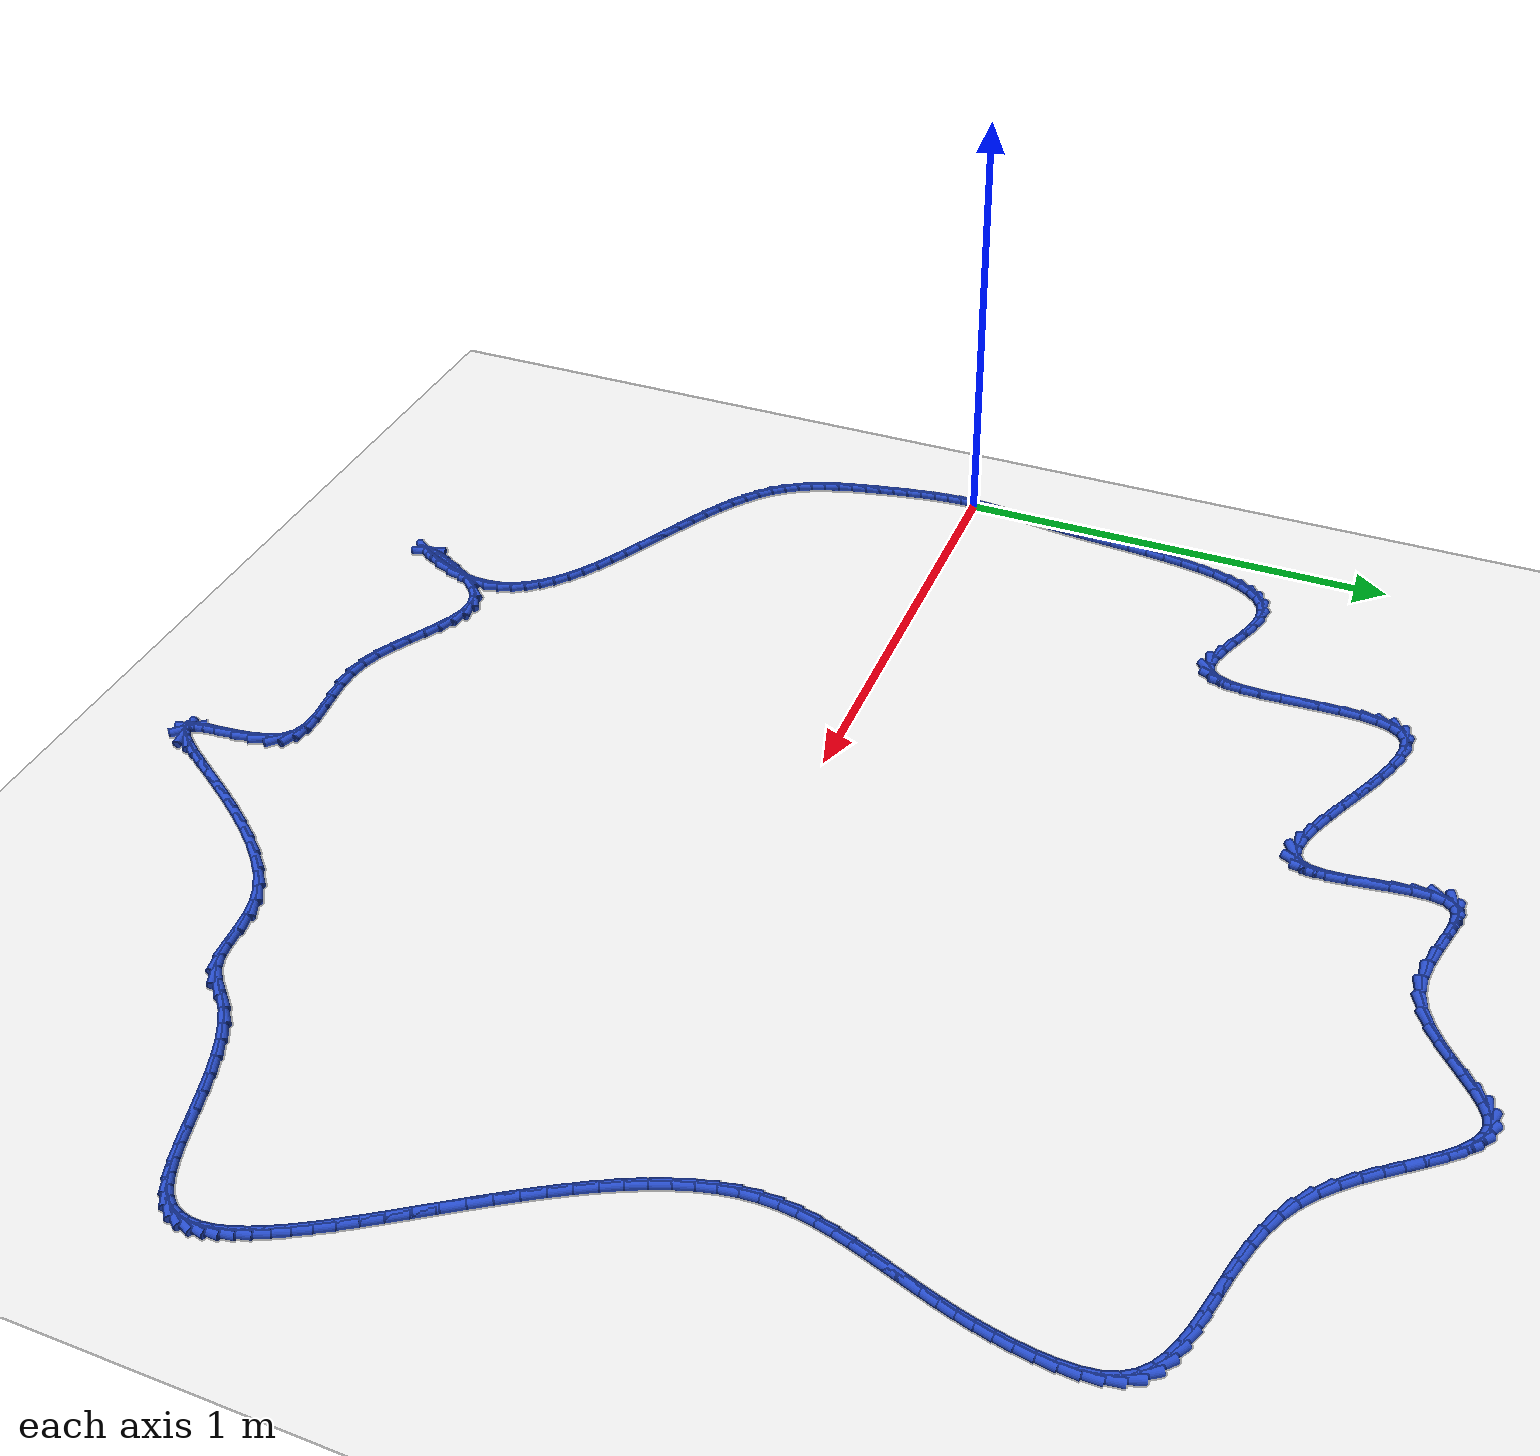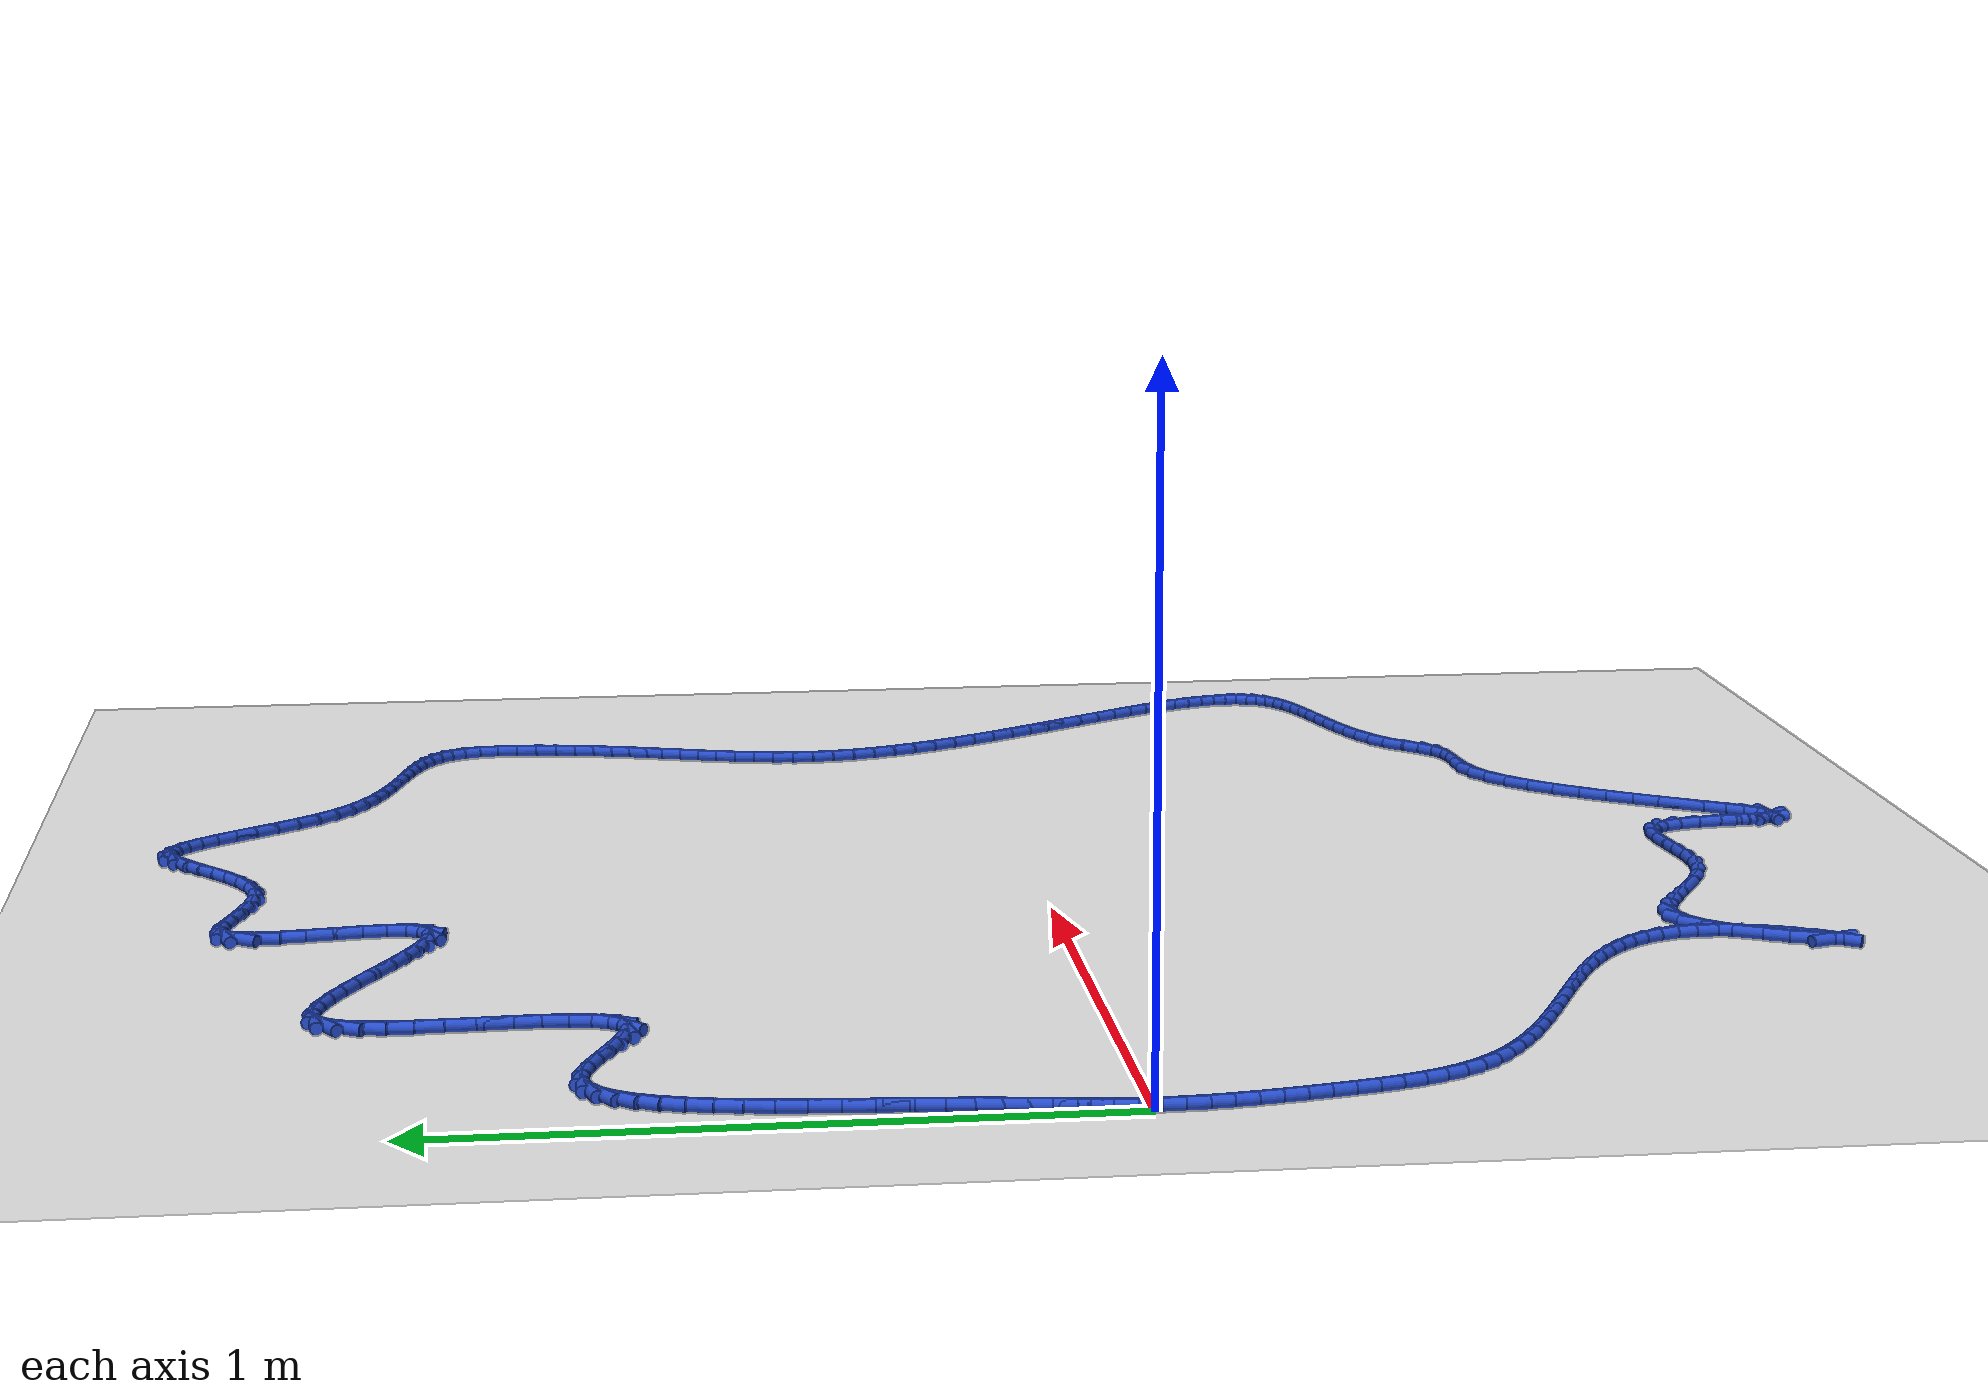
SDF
<sdf version="1.6">
 <world name="default">
  <light name="sun" type="directional">
   <pose>0 0 10 0 -0 0</pose>
   <diffuse>0.8 0.8 0.8 1</diffuse>
   <specular>0.2 0.2 0.2 1</specular>
   <attenuation>
    <range>1000</range>
    <constant>0.9</constant>
    <linear>0.01</linear>
    <quadratic>0.001</quadratic>
   </attenuation>
   <direction>-0.5 0.1 -0.9</direction>
  </light>
  <model name="ground_plane">
   <static>1</static>
   <link name="link">
    <collision name="collision">
     <geometry><plane><normal>0 0 1</normal><size>100 100</size></plane></geometry>
     <surface><friction><ode><mu>100</mu><mu2>50</mu2></ode></friction></surface>
    </collision>
    <visual name="visual">
     <cast_shadows>0</cast_shadows>
     <geometry><plane><normal>0 0 1</normal><size>100 100</size></plane></geometry>
     <material>
      <script><uri>file://media/materials/scripts/gazebo.material</uri><name>Gazebo/WhiteGlow</name></script>
     </material>
    </visual>
   </link>
  </model>
  <gravity>0 0 -9.8</gravity>
  <magnetic_field>6e-06 2.3e-05 -4.2e-05</magnetic_field>
  <atmosphere type="adiabatic"/>
  <physics name="default_physics" default="0" type="ode">
   <max_step_size>0.001</max_step_size>
   <real_time_factor>1</real_time_factor>
   <real_time_update_rate>1000</real_time_update_rate>
  </physics>
  <scene><ambient>0.4 0.4 0.4 1</ambient><background>0.7 0.7 0.7 1</background><shadows>1</shadows></scene>
  <spherical_coordinates>
   <surface_model>EARTH_WGS84</surface_model>
   <latitude_deg>0</latitude_deg>
   <longitude_deg>0</longitude_deg>
   <elevation>0</elevation>
   <heading_deg>0</heading_deg>
  </spherical_coordinates>
  <model name="line">
   <link name="link_0">
    <pose>1.734723475976807e-18 5.551115123125783e-17 0.01 0 1.57 1.5240284344869657</pose>
    <collision name="collision">
     <geometry><cylinder><radius>0.01</radius><length>0.08</length></cylinder></geometry>
    </collision>
    <visual name="visual">
     <material>
      <script><name>Gazebo/Blue</name><uri>file://media/materials/scripts/gazebo.material</uri></script>
     </material>
     <geometry><cylinder><radius>0.01</radius><length>0.08</length></cylinder></geometry>
    </visual>
   </link>
   <link name="link_1">
    <pose>0.0014910842718699158 0.03185940016066017 0.01 0 1.57 1.4774279963178367</pose>
    <collision name="collision">
     <geometry><cylinder><radius>0.01</radius><length>0.08</length></cylinder></geometry>
    </collision>
    <visual name="visual">
     <material>
      <script><name>Gazebo/Blue</name><uri>file://media/materials/scripts/gazebo.material</uri></script>
     </material>
     <geometry><cylinder><radius>0.01</radius><length>0.08</length></cylinder></geometry>
    </visual>
   </link>
   <link name="link_2">
    <pose>0.004453179364275393 0.06349199520359833 0.01 0 1.57 1.443887008379939</pose>
    <collision name="collision">
     <geometry><cylinder><radius>0.01</radius><length>0.08</length></cylinder></geometry>
    </collision>
    <visual name="visual">
     <material>
      <script><name>Gazebo/Blue</name><uri>file://media/materials/scripts/gazebo.material</uri></script>
     </material>
     <geometry><cylinder><radius>0.01</radius><length>0.08</length></cylinder></geometry>
    </visual>
   </link>
   <link name="link_3">
    <pose>0.008521601685281743 0.09537741475801953 0.01 0 1.57 1.4243843772346196</pose>
    <collision name="collision">
     <geometry><cylinder><radius>0.01</radius><length>0.08</length></cylinder></geometry>
    </collision>
    <visual name="visual">
     <material>
      <script><name>Gazebo/Blue</name><uri>file://media/materials/scripts/gazebo.material</uri></script>
     </material>
     <geometry><cylinder><radius>0.01</radius><length>0.08</length></cylinder></geometry>
    </visual>
   </link>
   <link name="link_4">
    <pose>0.013331667642954273 0.1279952884531287 0.01 0 1.57 1.418654762533308</pose>
    <collision name="collision">
     <geometry><cylinder><radius>0.01</radius><length>0.08</length></cylinder></geometry>
    </collision>
    <visual name="visual">
     <material>
      <script><name>Gazebo/Blue</name><uri>file://media/materials/scripts/gazebo.material</uri></script>
     </material>
     <geometry><cylinder><radius>0.01</radius><length>0.08</length></cylinder></geometry>
    </visual>
   </link>
   <link name="link_5">
    <pose>0.018518693645358294 0.16182524591813086 0.01 0 1.57 1.4254585022880335</pose>
    <collision name="collision">
     <geometry><cylinder><radius>0.01</radius><length>0.08</length></cylinder></geometry>
    </collision>
    <visual name="visual">
     <material>
      <script><name>Gazebo/Blue</name><uri>file://media/materials/scripts/gazebo.material</uri></script>
     </material>
     <geometry><cylinder><radius>0.01</radius><length>0.08</length></cylinder></geometry>
    </visual>
   </link>
   <link name="link_6">
    <pose>0.023717996100559108 0.19734691678223096 0.01 0 1.57 1.4429094265668516</pose>
    <collision name="collision">
     <geometry><cylinder><radius>0.01</radius><length>0.08</length></cylinder></geometry>
    </collision>
    <visual name="visual">
     <material>
      <script><name>Gazebo/Blue</name><uri>file://media/materials/scripts/gazebo.material</uri></script>
     </material>
     <geometry><cylinder><radius>0.01</radius><length>0.08</length></cylinder></geometry>
    </visual>
   </link>
   <link name="link_7">
    <pose>0.028564891416622034 0.2350399306746339 0.01 0 1.57 1.4664914685075665</pose>
    <collision name="collision">
     <geometry><cylinder><radius>0.01</radius><length>0.08</length></cylinder></geometry>
    </collision>
    <visual name="visual">
     <material>
      <script><name>Gazebo/Blue</name><uri>file://media/materials/scripts/gazebo.material</uri></script>
     </material>
     <geometry><cylinder><radius>0.01</radius><length>0.08</length></cylinder></geometry>
    </visual>
   </link>
   <link name="link_8">
    <pose>0.032773942285463 0.2752468369233878 0.01 0 1.57 1.4829178304906576</pose>
    <collision name="collision">
     <geometry><cylinder><radius>0.01</radius><length>0.08</length></cylinder></geometry>
    </collision>
    <visual name="visual">
     <material>
      <script><name>Gazebo/Blue</name><uri>file://media/materials/scripts/gazebo.material</uri></script>
     </material>
     <geometry><cylinder><radius>0.01</radius><length>0.08</length></cylinder></geometry>
    </visual>
   </link>
   <link name="link_9">
    <pose>0.03650082810726461 0.31754714073287466 0.01 0 1.57 1.4896878176367092</pose>
    <collision name="collision">
     <geometry><cylinder><radius>0.01</radius><length>0.08</length></cylinder></geometry>
    </collision>
    <visual name="visual">
     <material>
      <script><name>Gazebo/Blue</name><uri>file://media/materials/scripts/gazebo.material</uri></script>
     </material>
     <geometry><cylinder><radius>0.01</radius><length>0.08</length></cylinder></geometry>
    </visual>
   </link>
   <link name="link_10">
    <pose>0.040053815713403836 0.361256401416205 0.01 0 1.57 1.4879968515611792</pose>
    <collision name="collision">
     <geometry><cylinder><radius>0.01</radius><length>0.08</length></cylinder></geometry>
    </collision>
    <visual name="visual">
     <material>
      <script><name>Gazebo/Blue</name><uri>file://media/materials/scripts/gazebo.material</uri></script>
     </material>
     <geometry><cylinder><radius>0.01</radius><length>0.08</length></cylinder></geometry>
    </visual>
   </link>
   <link name="link_11">
    <pose>0.043741318808968616 0.4056899242241976 0.01 0 1.57 1.478187125413041</pose>
    <collision name="collision">
     <geometry><cylinder><radius>0.01</radius><length>0.08</length></cylinder></geometry>
    </collision>
    <visual name="visual">
     <material>
      <script><name>Gazebo/Blue</name><uri>file://media/materials/scripts/gazebo.material</uri></script>
     </material>
     <geometry><cylinder><radius>0.01</radius><length>0.08</length></cylinder></geometry>
    </visual>
   </link>
   <link name="link_12">
    <pose>0.04787175109904686 0.4501630144076707 0.01 0 1.57 1.4598686201475548</pose>
    <collision name="collision">
     <geometry><cylinder><radius>0.01</radius><length>0.08</length></cylinder></geometry>
    </collision>
    <visual name="visual">
     <material>
      <script><name>Gazebo/Blue</name><uri>file://media/materials/scripts/gazebo.material</uri></script>
     </material>
     <geometry><cylinder><radius>0.01</radius><length>0.08</length></cylinder></geometry>
    </visual>
   </link>
   <link name="link_13">
    <pose>0.05275352628872648 0.4939909772174427 0.01 0 1.57 1.4318898131964048</pose>
    <collision name="collision">
     <geometry><cylinder><radius>0.01</radius><length>0.08</length></cylinder></geometry>
    </collision>
    <visual name="visual">
     <material>
      <script><name>Gazebo/Blue</name><uri>file://media/materials/scripts/gazebo.material</uri></script>
     </material>
     <geometry><cylinder><radius>0.01</radius><length>0.08</length></cylinder></geometry>
    </visual>
   </link>
   <link name="link_14">
    <pose>0.05869505808309543 0.5364891179043322 0.01 0 1.57 1.3921615187901617</pose>
    <collision name="collision">
     <geometry><cylinder><radius>0.01</radius><length>0.08</length></cylinder></geometry>
    </collision>
    <visual name="visual">
     <material>
      <script><name>Gazebo/Blue</name><uri>file://media/materials/scripts/gazebo.material</uri></script>
     </material>
     <geometry><cylinder><radius>0.01</radius><length>0.08</length></cylinder></geometry>
    </visual>
   </link>
   <link name="link_15">
    <pose>0.0660047601872416 0.5769727417191575 0.01 0 1.57 1.3373036843806707</pose>
    <collision name="collision">
     <geometry><cylinder><radius>0.01</radius><length>0.08</length></cylinder></geometry>
    </collision>
    <visual name="visual">
     <material>
      <script><name>Gazebo/Blue</name><uri>file://media/materials/scripts/gazebo.material</uri></script>
     </material>
     <geometry><cylinder><radius>0.01</radius><length>0.08</length></cylinder></geometry>
    </visual>
   </link>
   <link name="link_16">
    <pose>0.07499104630625293 0.6147571539127371 0.01 0 1.57 1.262066126437284</pose>
    <collision name="collision">
     <geometry><cylinder><radius>0.01</radius><length>0.08</length></cylinder></geometry>
    </collision>
    <visual name="visual">
     <material>
      <script><name>Gazebo/Blue</name><uri>file://media/materials/scripts/gazebo.material</uri></script>
     </material>
     <geometry><cylinder><radius>0.01</radius><length>0.08</length></cylinder></geometry>
    </visual>
   </link>
   <link name="link_17">
    <pose>0.08596233014521734 0.6491576597358895 0.01 0 1.57 1.1585384522899038</pose>
    <collision name="collision">
     <geometry><cylinder><radius>0.01</radius><length>0.08</length></cylinder></geometry>
    </collision>
    <visual name="visual">
     <material>
      <script><name>Gazebo/Blue</name><uri>file://media/materials/scripts/gazebo.material</uri></script>
     </material>
     <geometry><cylinder><radius>0.01</radius><length>0.08</length></cylinder></geometry>
    </visual>
   </link>
   <link name="link_18">
    <pose>0.09922702540922274 0.679489564439433 0.01 0 1.57 1.0155808414627308</pose>
    <collision name="collision">
     <geometry><cylinder><radius>0.01</radius><length>0.08</length></cylinder></geometry>
    </collision>
    <visual name="visual">
     <material>
      <script><name>Gazebo/Blue</name><uri>file://media/materials/scripts/gazebo.material</uri></script>
     </material>
     <geometry><cylinder><radius>0.01</radius><length>0.08</length></cylinder></geometry>
    </visual>
   </link>
   <link name="link_19">
    <pose>0.11509354580335707 0.7050681732741864 0.01 0 1.57 0.8204288141330384</pose>
    <collision name="collision">
     <geometry><cylinder><radius>0.01</radius><length>0.08</length></cylinder></geometry>
    </collision>
    <visual name="visual">
     <material>
      <script><name>Gazebo/Blue</name><uri>file://media/materials/scripts/gazebo.material</uri></script>
     </material>
     <geometry><cylinder><radius>0.01</radius><length>0.08</length></cylinder></geometry>
    </visual>
   </link>
   <link name="link_20">
    <pose>0.13387030503270822 0.7252087914909674 0.01 0 1.57 0.5674037125127195</pose>
    <collision name="collision">
     <geometry><cylinder><radius>0.01</radius><length>0.08</length></cylinder></geometry>
    </collision>
    <visual name="visual">
     <material>
      <script><name>Gazebo/Blue</name><uri>file://media/materials/scripts/gazebo.material</uri></script>
     </material>
     <geometry><cylinder><radius>0.01</radius><length>0.08</length></cylinder></geometry>
    </visual>
   </link>
   <link name="link_21">
    <pose>0.15586571680236416 0.7392267243405953 0.01 0 1.57 0.27534187046365877</pose>
    <collision name="collision">
     <geometry><cylinder><radius>0.01</radius><length>0.08</length></cylinder></geometry>
    </collision>
    <visual name="visual">
     <material>
      <script><name>Gazebo/Blue</name><uri>file://media/materials/scripts/gazebo.material</uri></script>
     </material>
     <geometry><cylinder><radius>0.01</radius><length>0.08</length></cylinder></geometry>
    </visual>
   </link>
   <link name="link_22">
    <pose>0.1813881948174128 0.746437277073888 0.01 0 1.57 -0.009588929353175622</pose>
    <collision name="collision">
     <geometry><cylinder><radius>0.01</radius><length>0.08</length></cylinder></geometry>
    </collision>
    <visual name="visual">
     <material>
      <script><name>Gazebo/Blue</name><uri>file://media/materials/scripts/gazebo.material</uri></script>
     </material>
     <geometry><cylinder><radius>0.01</radius><length>0.08</length></cylinder></geometry>
    </visual>
   </link>
   <link name="link_23">
    <pose>0.21074615160790677 0.7461557570718578 0.01 0 1.57 -0.23177906006464233</pose>
    <collision name="collision">
     <geometry><cylinder><radius>0.01</radius><length>0.08</length></cylinder></geometry>
    </collision>
    <visual name="visual">
     <material>
      <script><name>Gazebo/Blue</name><uri>file://media/materials/scripts/gazebo.material</uri></script>
     </material>
     <geometry><cylinder><radius>0.01</radius><length>0.08</length></cylinder></geometry>
    </visual>
   </link>
   <link name="link_24">
    <pose>0.2438984722624785 0.7383311218168889 0.01 0 1.57 -0.3503277729756189</pose>
    <collision name="collision">
     <geometry><cylinder><radius>0.01</radius><length>0.08</length></cylinder></geometry>
    </collision>
    <visual name="visual">
     <material>
      <script><name>Gazebo/Blue</name><uri>file://media/materials/scripts/gazebo.material</uri></script>
     </material>
     <geometry><cylinder><radius>0.01</radius><length>0.08</length></cylinder></geometry>
    </visual>
   </link>
   <link name="link_25">
    <pose>0.27946827006113223 0.7253339181764713 0.01 0 1.57 -0.3971235530927722</pose>
    <collision name="collision">
     <geometry><cylinder><radius>0.01</radius><length>0.08</length></cylinder></geometry>
    </collision>
    <visual name="visual">
     <material>
      <script><name>Gazebo/Blue</name><uri>file://media/materials/scripts/gazebo.material</uri></script>
     </material>
     <geometry><cylinder><radius>0.01</radius><length>0.08</length></cylinder></geometry>
    </visual>
   </link>
   <link name="link_26">
    <pose>0.31575961091191423 0.710113086516362 0.01 0 1.57 -0.3894745904414337</pose>
    <collision name="collision">
     <geometry><cylinder><radius>0.01</radius><length>0.08</length></cylinder></geometry>
    </collision>
    <visual name="visual">
     <material>
      <script><name>Gazebo/Blue</name><uri>file://media/materials/scripts/gazebo.material</uri></script>
     </material>
     <geometry><cylinder><radius>0.01</radius><length>0.08</length></cylinder></geometry>
    </visual>
   </link>
   <link name="link_27">
    <pose>0.35107656072287097 0.6956175672023183 0.01 0 1.57 -0.320069579930596</pose>
    <collision name="collision">
     <geometry><cylinder><radius>0.01</radius><length>0.08</length></cylinder></geometry>
    </collision>
    <visual name="visual">
     <material>
      <script><name>Gazebo/Blue</name><uri>file://media/materials/scripts/gazebo.material</uri></script>
     </material>
     <geometry><cylinder><radius>0.01</radius><length>0.08</length></cylinder></geometry>
    </visual>
   </link>
   <link name="link_28">
    <pose>0.38372318540204886 0.6847963006000972 0.01 0 1.57 -0.14736863514359108</pose>
    <collision name="collision">
     <geometry><cylinder><radius>0.01</radius><length>0.08</length></cylinder></geometry>
    </collision>
    <visual name="visual">
     <material>
      <script><name>Gazebo/Blue</name><uri>file://media/materials/scripts/gazebo.material</uri></script>
     </material>
     <geometry><cylinder><radius>0.01</radius><length>0.08</length></cylinder></geometry>
    </visual>
   </link>
   <link name="link_29">
    <pose>0.4120035508574942 0.680598227075456 0.01 0 1.57 0.235723255302384</pose>
    <collision name="collision">
     <geometry><cylinder><radius>0.01</radius><length>0.08</length></cylinder></geometry>
    </collision>
    <visual name="visual">
     <material>
      <script><name>Gazebo/Blue</name><uri>file://media/materials/scripts/gazebo.material</uri></script>
     </material>
     <geometry><cylinder><radius>0.01</radius><length>0.08</length></cylinder></geometry>
    </visual>
   </link>
   <link name="link_30">
    <pose>0.4342413646948932 0.6859394953644006 0.01 0 1.57 0.7992052413507794</pose>
    <collision name="collision">
     <geometry><cylinder><radius>0.01</radius><length>0.08</length></cylinder></geometry>
    </collision>
    <visual name="visual">
     <material>
      <script><name>Gazebo/Blue</name><uri>file://media/materials/scripts/gazebo.material</uri></script>
     </material>
     <geometry><cylinder><radius>0.01</radius><length>0.08</length></cylinder></geometry>
    </visual>
   </link>
   <link name="link_31">
    <pose>0.4498247377898314 0.7019592429398303 0.01 0 1.57 1.1961392918587017</pose>
    <collision name="collision">
     <geometry><cylinder><radius>0.01</radius><length>0.08</length></cylinder></geometry>
    </collision>
    <visual name="visual">
     <material>
      <script><name>Gazebo/Blue</name><uri>file://media/materials/scripts/gazebo.material</uri></script>
     </material>
     <geometry><cylinder><radius>0.01</radius><length>0.08</length></cylinder></geometry>
    </visual>
   </link>
   <link name="link_32">
    <pose>0.45972914390245384 0.7271465198460642 0.01 0 1.57 1.4088559822709672</pose>
    <collision name="collision">
     <geometry><cylinder><radius>0.01</radius><length>0.08</length></cylinder></geometry>
    </collision>
    <visual name="visual">
     <material>
      <script><name>Gazebo/Blue</name><uri>file://media/materials/scripts/gazebo.material</uri></script>
     </material>
     <geometry><cylinder><radius>0.01</radius><length>0.08</length></cylinder></geometry>
    </visual>
   </link>
   <link name="link_33">
    <pose>0.4650595559600769 0.7597741784839765 0.01 0 1.57 1.5222859646955555</pose>
    <collision name="collision">
     <geometry><cylinder><radius>0.01</radius><length>0.08</length></cylinder></geometry>
    </collision>
    <visual name="visual">
     <material>
      <script><name>Gazebo/Blue</name><uri>file://media/materials/scripts/gazebo.material</uri></script>
     </material>
     <geometry><cylinder><radius>0.01</radius><length>0.08</length></cylinder></geometry>
    </visual>
   </link>
   <link name="link_34">
    <pose>0.46692094689001723 0.7981150712544434 0.01 0 1.57 -1.5589213087593814</pose>
    <collision name="collision">
     <geometry><cylinder><radius>0.01</radius><length>0.08</length></cylinder></geometry>
    </collision>
    <visual name="visual">
     <material>
      <script><name>Gazebo/Blue</name><uri>file://media/materials/scripts/gazebo.material</uri></script>
     </material>
     <geometry><cylinder><radius>0.01</radius><length>0.08</length></cylinder></geometry>
    </visual>
   </link>
   <link name="link_35">
    <pose>0.466418289619591 0.8404420505583386 0.01 0 1.57 -1.5313036660955552</pose>
    <collision name="collision">
     <geometry><cylinder><radius>0.01</radius><length>0.08</length></cylinder></geometry>
    </collision>
    <visual name="visual">
     <material>
      <script><name>Gazebo/Blue</name><uri>file://media/materials/scripts/gazebo.material</uri></script>
     </material>
     <geometry><cylinder><radius>0.01</radius><length>0.08</length></cylinder></geometry>
    </visual>
   </link>
   <link name="link_36">
    <pose>0.46465655707611453 0.8850279687965372 0.01 0 1.57 -1.528358785863385</pose>
    <collision name="collision">
     <geometry><cylinder><radius>0.01</radius><length>0.08</length></cylinder></geometry>
    </collision>
    <visual name="visual">
     <material>
      <script><name>Gazebo/Blue</name><uri>file://media/materials/scripts/gazebo.material</uri></script>
     </material>
     <geometry><cylinder><radius>0.01</radius><length>0.08</length></cylinder></geometry>
    </visual>
   </link>
   <link name="link_37">
    <pose>0.46274072218690454 0.9301456783699142 0.01 0 1.57 -1.5488300834947064</pose>
    <collision name="collision">
     <geometry><cylinder><radius>0.01</radius><length>0.08</length></cylinder></geometry>
    </collision>
    <visual name="visual">
     <material>
      <script><name>Gazebo/Blue</name><uri>file://media/materials/scripts/gazebo.material</uri></script>
     </material>
     <geometry><cylinder><radius>0.01</radius><length>0.08</length></cylinder></geometry>
    </visual>
   </link>
   <link name="link_38">
    <pose>0.4617757578792772 0.9740680316793452 0.01 0 1.57 1.5441956952280265</pose>
    <collision name="collision">
     <geometry><cylinder><radius>0.01</radius><length>0.08</length></cylinder></geometry>
    </collision>
    <visual name="visual">
     <material>
      <script><name>Gazebo/Blue</name><uri>file://media/materials/scripts/gazebo.material</uri></script>
     </material>
     <geometry><cylinder><radius>0.01</radius><length>0.08</length></cylinder></geometry>
    </visual>
   </link>
   <link name="link_39">
    <pose>0.462866637080549 1.015067881125704 0.01 0 1.57 1.4543605258313845</pose>
    <collision name="collision">
     <geometry><cylinder><radius>0.01</radius><length>0.08</length></cylinder></geometry>
    </collision>
    <visual name="visual">
     <material>
      <script><name>Gazebo/Blue</name><uri>file://media/materials/scripts/gazebo.material</uri></script>
     </material>
     <geometry><cylinder><radius>0.01</radius><length>0.08</length></cylinder></geometry>
    </visual>
   </link>
   <link name="link_40">
    <pose>0.46711833271803627 1.051418079109866 0.01 0 1.57 1.2939267069660565</pose>
    <collision name="collision">
     <geometry><cylinder><radius>0.01</radius><length>0.08</length></cylinder></geometry>
    </collision>
    <visual name="visual">
     <material>
      <script><name>Gazebo/Blue</name><uri>file://media/materials/scripts/gazebo.material</uri></script>
     </material>
     <geometry><cylinder><radius>0.01</radius><length>0.08</length></cylinder></geometry>
    </visual>
   </link>
   <link name="link_41">
    <pose>0.47563581771905544 1.0813914780327056 0.01 0 1.57 1.0050009832171045</pose>
    <collision name="collision">
     <geometry><cylinder><radius>0.01</radius><length>0.08</length></cylinder></geometry>
    </collision>
    <visual name="visual">
     <material>
      <script><name>Gazebo/Blue</name><uri>file://media/materials/scripts/gazebo.material</uri></script>
     </material>
     <geometry><cylinder><radius>0.01</radius><length>0.08</length></cylinder></geometry>
    </visual>
   </link>
   <link name="link_42">
    <pose>0.48952406501092294 1.1032609302950986 0.01 0 1.57 0.5401077132505143</pose>
    <collision name="collision">
     <geometry><cylinder><radius>0.01</radius><length>0.08</length></cylinder></geometry>
    </collision>
    <visual name="visual">
     <material>
      <script><name>Gazebo/Blue</name><uri>file://media/materials/scripts/gazebo.material</uri></script>
     </material>
     <geometry><cylinder><radius>0.01</radius><length>0.08</length></cylinder></geometry>
    </visual>
   </link>
   <link name="link_43">
    <pose>0.509806724819831 1.1154219273254888 0.01 0 1.57 0.09911444449227311</pose>
    <collision name="collision">
     <geometry><cylinder><radius>0.01</radius><length>0.08</length></cylinder></geometry>
    </collision>
    <visual name="visual">
     <material>
      <script><name>Gazebo/Blue</name><uri>file://media/materials/scripts/gazebo.material</uri></script>
     </material>
     <geometry><cylinder><radius>0.01</radius><length>0.08</length></cylinder></geometry>
    </visual>
   </link>
   <link name="link_44">
    <pose>0.536321418665322 1.118058555929035 0.01 0 1.57 -0.1672673672036123</pose>
    <collision name="collision">
     <geometry><cylinder><radius>0.01</radius><length>0.08</length></cylinder></geometry>
    </collision>
    <visual name="visual">
     <material>
      <script><name>Gazebo/Blue</name><uri>file://media/materials/scripts/gazebo.material</uri></script>
     </material>
     <geometry><cylinder><radius>0.01</radius><length>0.08</length></cylinder></geometry>
    </visual>
   </link>
   <link name="link_45">
    <pose>0.5680082613288457 1.1127083915687388 0.01 0 1.57 -0.3177267045697395</pose>
    <collision name="collision">
     <geometry><cylinder><radius>0.01</radius><length>0.08</length></cylinder></geometry>
    </collision>
    <visual name="visual">
     <material>
      <script><name>Gazebo/Blue</name><uri>file://media/materials/scripts/gazebo.material</uri></script>
     </material>
     <geometry><cylinder><radius>0.01</radius><length>0.08</length></cylinder></geometry>
    </visual>
   </link>
   <link name="link_46">
    <pose>0.6037851584369688 1.1009425023132355 0.01 0 1.57 -0.4046404868182337</pose>
    <collision name="collision">
     <geometry><cylinder><radius>0.01</radius><length>0.08</length></cylinder></geometry>
    </collision>
    <visual name="visual">
     <material>
      <script><name>Gazebo/Blue</name><uri>file://media/materials/scripts/gazebo.material</uri></script>
     </material>
     <geometry><cylinder><radius>0.01</radius><length>0.08</length></cylinder></geometry>
    </visual>
   </link>
   <link name="link_47">
    <pose>0.642570015616258 1.0843319562311602 0.01 0 1.57 -0.4543448045155918</pose>
    <collision name="collision">
     <geometry><cylinder><radius>0.01</radius><length>0.08</length></cylinder></geometry>
    </collision>
    <visual name="visual">
     <material>
      <script><name>Gazebo/Blue</name><uri>file://media/materials/scripts/gazebo.material</uri></script>
     </material>
     <geometry><cylinder><radius>0.01</radius><length>0.08</length></cylinder></geometry>
    </visual>
   </link>
   <link name="link_48">
    <pose>0.6832807384932802 1.064447821391149 0.01 0 1.57 -0.4791084993262882</pose>
    <collision name="collision">
     <geometry><cylinder><radius>0.01</radius><length>0.08</length></cylinder></geometry>
    </collision>
    <visual name="visual">
     <material>
      <script><name>Gazebo/Blue</name><uri>file://media/materials/scripts/gazebo.material</uri></script>
     </material>
     <geometry><cylinder><radius>0.01</radius><length>0.08</length></cylinder></geometry>
    </visual>
   </link>
   <link name="link_49">
    <pose>0.7248352326946021 1.0428611658618376 0.01 0 1.57 -0.4839614027424454</pose>
    <collision name="collision">
     <geometry><cylinder><radius>0.01</radius><length>0.08</length></cylinder></geometry>
    </collision>
    <visual name="visual">
     <material>
      <script><name>Gazebo/Blue</name><uri>file://media/materials/scripts/gazebo.material</uri></script>
     </material>
     <geometry><cylinder><radius>0.01</radius><length>0.08</length></cylinder></geometry>
    </visual>
   </link>
   <link name="link_50">
    <pose>0.7661514038467914 1.0211430577118619 0.01 0 1.57 -0.469244754834158</pose>
    <collision name="collision">
     <geometry><cylinder><radius>0.01</radius><length>0.08</length></cylinder></geometry>
    </collision>
    <visual name="visual">
     <material>
      <script><name>Gazebo/Blue</name><uri>file://media/materials/scripts/gazebo.material</uri></script>
     </material>
     <geometry><cylinder><radius>0.01</radius><length>0.08</length></cylinder></geometry>
    </visual>
   </link>
   <link name="link_51">
    <pose>0.8061471575764142 1.0008645650098564 0.01 0 1.57 -0.4305879268047215</pose>
    <collision name="collision">
     <geometry><cylinder><radius>0.01</radius><length>0.08</length></cylinder></geometry>
    </collision>
    <visual name="visual">
     <material>
      <script><name>Gazebo/Blue</name><uri>file://media/materials/scripts/gazebo.material</uri></script>
     </material>
     <geometry><cylinder><radius>0.01</radius><length>0.08</length></cylinder></geometry>
    </visual>
   </link>
   <link name="link_52">
    <pose>0.8437403995100371 0.9835967558244579 0.01 0 1.57 -0.3560772928252433</pose>
    <collision name="collision">
     <geometry><cylinder><radius>0.01</radius><length>0.08</length></cylinder></geometry>
    </collision>
    <visual name="visual">
     <material>
      <script><name>Gazebo/Blue</name><uri>file://media/materials/scripts/gazebo.material</uri></script>
     </material>
     <geometry><cylinder><radius>0.01</radius><length>0.08</length></cylinder></geometry>
    </visual>
   </link>
   <link name="link_53">
    <pose>0.8778490352742276 0.9709106982243018 0.01 0 1.57 -0.2176482071715738</pose>
    <collision name="collision">
     <geometry><cylinder><radius>0.01</radius><length>0.08</length></cylinder></geometry>
    </collision>
    <visual name="visual">
     <material>
      <script><name>Gazebo/Blue</name><uri>file://media/materials/scripts/gazebo.material</uri></script>
     </material>
     <geometry><cylinder><radius>0.01</radius><length>0.08</length></cylinder></geometry>
    </visual>
   </link>
   <link name="link_54">
    <pose>0.9073909704955525 0.9643774602780233 0.01 0 1.57 0.049791097524645965</pose>
    <collision name="collision">
     <geometry><cylinder><radius>0.01</radius><length>0.08</length></cylinder></geometry>
    </collision>
    <visual name="visual">
     <material>
      <script><name>Gazebo/Blue</name><uri>file://media/materials/scripts/gazebo.material</uri></script>
     </material>
     <geometry><cylinder><radius>0.01</radius><length>0.08</length></cylinder></geometry>
    </visual>
   </link>
   <link name="link_55">
    <pose>0.9312841108005785 0.9655681100542584 0.01 0 1.57 0.5484460207274386</pose>
    <collision name="collision">
     <geometry><cylinder><radius>0.01</radius><length>0.08</length></cylinder></geometry>
    </collision>
    <visual name="visual">
     <material>
      <script><name>Gazebo/Blue</name><uri>file://media/materials/scripts/gazebo.material</uri></script>
     </material>
     <geometry><cylinder><radius>0.01</radius><length>0.08</length></cylinder></geometry>
    </visual>
   </link>
   <link name="link_56">
    <pose>0.9484463618158725 0.9760537156216427 0.01 0 1.57 1.149002849617359</pose>
    <collision name="collision">
     <geometry><cylinder><radius>0.01</radius><length>0.08</length></cylinder></geometry>
    </collision>
    <visual name="visual">
     <material>
      <script><name>Gazebo/Blue</name><uri>file://media/materials/scripts/gazebo.material</uri></script>
     </material>
     <geometry><cylinder><radius>0.01</radius><length>0.08</length></cylinder></geometry>
    </visual>
   </link>
   <link name="link_57">
    <pose>0.9579377813561684 0.9972056699392743 0.01 0 1.57 1.4845202666143227</pose>
    <collision name="collision">
     <geometry><cylinder><radius>0.01</radius><length>0.08</length></cylinder></geometry>
    </collision>
    <visual name="visual">
     <material>
      <script><name>Gazebo/Blue</name><uri>file://media/materials/scripts/gazebo.material</uri></script>
     </material>
     <geometry><cylinder><radius>0.01</radius><length>0.08</length></cylinder></geometry>
    </visual>
   </link>
   <link name="link_58">
    <pose>0.9605928136043744 1.027902961192226 0.01 0 1.57 -1.5136430494704942</pose>
    <collision name="collision">
     <geometry><cylinder><radius>0.01</radius><length>0.08</length></cylinder></geometry>
    </collision>
    <visual name="visual">
     <material>
      <script><name>Gazebo/Blue</name><uri>file://media/materials/scripts/gazebo.material</uri></script>
     </material>
     <geometry><cylinder><radius>0.01</radius><length>0.08</length></cylinder></geometry>
    </visual>
   </link>
   <link name="link_59">
    <pose>0.9584513250103387 1.0653313723726479 0.01 0 1.57 -1.453334506921732</pose>
    <collision name="collision">
     <geometry><cylinder><radius>0.01</radius><length>0.08</length></cylinder></geometry>
    </collision>
    <visual name="visual">
     <material>
      <script><name>Gazebo/Blue</name><uri>file://media/materials/scripts/gazebo.material</uri></script>
     </material>
     <geometry><cylinder><radius>0.01</radius><length>0.08</length></cylinder></geometry>
    </visual>
   </link>
   <link name="link_60">
    <pose>0.9535761821625041 1.1066443791599965 0.01 0 1.57 -1.4405859051673429</pose>
    <collision name="collision">
     <geometry><cylinder><radius>0.01</radius><length>0.08</length></cylinder></geometry>
    </collision>
    <visual name="visual">
     <material>
      <script><name>Gazebo/Blue</name><uri>file://media/materials/scripts/gazebo.material</uri></script>
     </material>
     <geometry><cylinder><radius>0.01</radius><length>0.08</length></cylinder></geometry>
    </visual>
   </link>
   <link name="link_61">
    <pose>0.9480302516493135 1.1489954572337304 0.01 0 1.57 -1.4686961868022166</pose>
    <collision name="collision">
     <geometry><cylinder><radius>0.01</radius><length>0.08</length></cylinder></geometry>
    </collision>
    <visual name="visual">
     <material>
      <script><name>Gazebo/Blue</name><uri>file://media/materials/scripts/gazebo.material</uri></script>
     </material>
     <geometry><cylinder><radius>0.01</radius><length>0.08</length></cylinder></geometry>
    </visual>
   </link>
   <link name="link_62">
    <pose>0.9438764000592097 1.1895380822733064 0.01 0 1.57 -1.5513239515936352</pose>
    <collision name="collision">
     <geometry><cylinder><radius>0.01</radius><length>0.08</length></cylinder></geometry>
    </collision>
    <visual name="visual">
     <material>
      <script><name>Gazebo/Blue</name><uri>file://media/materials/scripts/gazebo.material</uri></script>
     </material>
     <geometry><cylinder><radius>0.01</radius><length>0.08</length></cylinder></geometry>
    </visual>
   </link>
   <link name="link_63">
    <pose>0.9431774939806357 1.225425729958181 0.01 0 1.57 1.4026369081183898</pose>
    <collision name="collision">
     <geometry><cylinder><radius>0.01</radius><length>0.08</length></cylinder></geometry>
    </collision>
    <visual name="visual">
     <material>
      <script><name>Gazebo/Blue</name><uri>file://media/materials/scripts/gazebo.material</uri></script>
     </material>
     <geometry><cylinder><radius>0.01</radius><length>0.08</length></cylinder></geometry>
    </visual>
   </link>
   <link name="link_64">
    <pose>0.9479964000020334 1.2538118759678112 0.01 0 1.57 0.9688243990664752</pose>
    <collision name="collision">
     <geometry><cylinder><radius>0.01</radius><length>0.08</length></cylinder></geometry>
    </collision>
    <visual name="visual">
     <material>
      <script><name>Gazebo/Blue</name><uri>file://media/materials/scripts/gazebo.material</uri></script>
     </material>
     <geometry><cylinder><radius>0.01</radius><length>0.08</length></cylinder></geometry>
    </visual>
   </link>
   <link name="link_65">
    <pose>0.9603927671434382 1.271855143567124 0.01 0 1.57 0.2981875370096735</pose>
    <collision name="collision">
     <geometry><cylinder><radius>0.01</radius><length>0.08</length></cylinder></geometry>
    </collision>
    <visual name="visual">
     <material>
      <script><name>Gazebo/Blue</name><uri>file://media/materials/scripts/gazebo.material</uri></script>
     </material>
     <geometry><cylinder><radius>0.01</radius><length>0.08</length></cylinder></geometry>
    </visual>
   </link>
   <link name="link_66">
    <pose>0.9814231925790543 1.2783188756263189 0.01 0 1.57 -0.08738735991662325</pose>
    <collision name="collision">
     <geometry><cylinder><radius>0.01</radius><length>0.08</length></cylinder></geometry>
    </collision>
    <visual name="visual">
     <material>
      <script><name>Gazebo/Blue</name><uri>file://media/materials/scripts/gazebo.material</uri></script>
     </material>
     <geometry><cylinder><radius>0.01</radius><length>0.08</length></cylinder></geometry>
    </visual>
   </link>
   <link name="link_67">
    <pose>1.0097233587953658 1.2758394842674308 0.01 0 1.57 -0.23805824030081318</pose>
    <collision name="collision">
     <geometry><cylinder><radius>0.01</radius><length>0.08</length></cylinder></geometry>
    </collision>
    <visual name="visual">
     <material>
      <script><name>Gazebo/Blue</name><uri>file://media/materials/scripts/gazebo.material</uri></script>
     </material>
     <geometry><cylinder><radius>0.01</radius><length>0.08</length></cylinder></geometry>
    </visual>
   </link>
   <link name="link_68">
    <pose>1.0435710092084798 1.2676260258343406 0.01 0 1.57 -0.27768086560515354</pose>
    <collision name="collision">
     <geometry><cylinder><radius>0.01</radius><length>0.08</length></cylinder></geometry>
    </collision>
    <visual name="visual">
     <material>
      <script><name>Gazebo/Blue</name><uri>file://media/materials/scripts/gazebo.material</uri></script>
     </material>
     <geometry><cylinder><radius>0.01</radius><length>0.08</length></cylinder></geometry>
    </visual>
   </link>
   <link name="link_69">
    <pose>1.0812438872345045 1.2568875566709294 0.01 0 1.57 -0.24759068626663827</pose>
    <collision name="collision">
     <geometry><cylinder><radius>0.01</radius><length>0.08</length></cylinder></geometry>
    </collision>
    <visual name="visual">
     <material>
      <script><name>Gazebo/Blue</name><uri>file://media/materials/scripts/gazebo.material</uri></script>
     </material>
     <geometry><cylinder><radius>0.01</radius><length>0.08</length></cylinder></geometry>
    </visual>
   </link>
   <link name="link_70">
    <pose>1.1210197362895482 1.2468331331210767 0.01 0 1.57 -0.152245205504104</pose>
    <collision name="collision">
     <geometry><cylinder><radius>0.01</radius><length>0.08</length></cylinder></geometry>
    </collision>
    <visual name="visual">
     <material>
      <script><name>Gazebo/Blue</name><uri>file://media/materials/scripts/gazebo.material</uri></script>
     </material>
     <geometry><cylinder><radius>0.01</radius><length>0.08</length></cylinder></geometry>
    </visual>
   </link>
   <link name="link_71">
    <pose>1.1611762997897181 1.2406718115286641 0.01 0 1.57 0.023915282053574946</pose>
    <collision name="collision">
     <geometry><cylinder><radius>0.01</radius><length>0.08</length></cylinder></geometry>
    </collision>
    <visual name="visual">
     <material>
      <script><name>Gazebo/Blue</name><uri>file://media/materials/scripts/gazebo.material</uri></script>
     </material>
     <geometry><cylinder><radius>0.01</radius><length>0.08</length></cylinder></geometry>
    </visual>
   </link>
   <link name="link_72">
    <pose>1.199995699316528 1.24160036545018 0.01 0 1.57 0.2569513364190894</pose>
    <collision name="collision">
     <geometry><cylinder><radius>0.01</radius><length>0.08</length></cylinder></geometry>
    </collision>
    <visual name="visual">
     <material>
      <script><name>Gazebo/Blue</name><uri>file://media/materials/scripts/gazebo.material</uri></script>
     </material>
     <geometry><cylinder><radius>0.01</radius><length>0.08</length></cylinder></geometry>
    </visual>
   </link>
   <link name="link_73">
    <pose>1.2363525062563927 1.2511534715775552 0.01 0 1.57 0.4495954709208607</pose>
    <collision name="collision">
     <geometry><cylinder><radius>0.01</radius><length>0.08</length></cylinder></geometry>
    </collision>
    <visual name="visual">
     <material>
      <script><name>Gazebo/Blue</name><uri>file://media/materials/scripts/gazebo.material</uri></script>
     </material>
     <geometry><cylinder><radius>0.01</radius><length>0.08</length></cylinder></geometry>
    </visual>
   </link>
   <link name="link_74">
    <pose>1.2703072799655477 1.2675385595182629 0.01 0 1.57 0.5849057528706614</pose>
    <collision name="collision">
     <geometry><cylinder><radius>0.01</radius><length>0.08</length></cylinder></geometry>
    </collision>
    <visual name="visual">
     <material>
      <script><name>Gazebo/Blue</name><uri>file://media/materials/scripts/gazebo.material</uri></script>
     </material>
     <geometry><cylinder><radius>0.01</radius><length>0.08</length></cylinder></geometry>
    </visual>
   </link>
   <link name="link_75">
    <pose>1.3020619107705766 1.2885665598671405 0.01 0 1.57 0.668081648597988</pose>
    <collision name="collision">
     <geometry><cylinder><radius>0.01</radius><length>0.08</length></cylinder></geometry>
    </collision>
    <visual name="visual">
     <material>
      <script><name>Gazebo/Blue</name><uri>file://media/materials/scripts/gazebo.material</uri></script>
     </material>
     <geometry><cylinder><radius>0.01</radius><length>0.08</length></cylinder></geometry>
    </visual>
   </link>
   <link name="link_76">
    <pose>1.3318182889980608 1.3120484032190252 0.01 0 1.57 0.7040911818214479</pose>
    <collision name="collision">
     <geometry><cylinder><radius>0.01</radius><length>0.08</length></cylinder></geometry>
    </collision>
    <visual name="visual">
     <material>
      <script><name>Gazebo/Blue</name><uri>file://media/materials/scripts/gazebo.material</uri></script>
     </material>
     <geometry><cylinder><radius>0.01</radius><length>0.08</length></cylinder></geometry>
    </visual>
   </link>
   <link name="link_77">
    <pose>1.3597783049745833 1.335795020168755 0.01 0 1.57 0.6913945657915324</pose>
    <collision name="collision">
     <geometry><cylinder><radius>0.01</radius><length>0.08</length></cylinder></geometry>
    </collision>
    <visual name="visual">
     <material>
      <script><name>Gazebo/Blue</name><uri>file://media/materials/scripts/gazebo.material</uri></script>
     </material>
     <geometry><cylinder><radius>0.01</radius><length>0.08</length></cylinder></geometry>
    </visual>
   </link>
   <link name="link_78">
    <pose>1.3861438490267284 1.357617341311168 0.01 0 1.57 0.6168240129013752</pose>
    <collision name="collision">
     <geometry><cylinder><radius>0.01</radius><length>0.08</length></cylinder></geometry>
    </collision>
    <visual name="visual">
     <material>
      <script><name>Gazebo/Blue</name><uri>file://media/materials/scripts/gazebo.material</uri></script>
     </material>
     <geometry><cylinder><radius>0.01</radius><length>0.08</length></cylinder></geometry>
    </visual>
   </link>
   <link name="link_79">
    <pose>1.4111168114810768 1.3753262972411013 0.01 0 1.57 0.44721342519376794</pose>
    <collision name="collision">
     <geometry><cylinder><radius>0.01</radius><length>0.08</length></cylinder></geometry>
    </collision>
    <visual name="visual">
     <material>
      <script><name>Gazebo/Blue</name><uri>file://media/materials/scripts/gazebo.material</uri></script>
     </material>
     <geometry><cylinder><radius>0.01</radius><length>0.08</length></cylinder></geometry>
    </visual>
   </link>
   <link name="link_80">
    <pose>1.4348990826642116 1.3867328185533927 0.01 0 1.57 0.1313487871875756</pose>
    <collision name="collision">
     <geometry><cylinder><radius>0.01</radius><length>0.08</length></cylinder></geometry>
    </collision>
    <visual name="visual">
     <material>
      <script><name>Gazebo/Blue</name><uri>file://media/materials/scripts/gazebo.material</uri></script>
     </material>
     <geometry><cylinder><radius>0.01</radius><length>0.08</length></cylinder></geometry>
    </visual>
   </link>
   <link name="link_81">
    <pose>1.4576952057606638 1.3897444007384727 0.01 0 1.57 -0.2539176233739792</pose>
    <collision name="collision">
     <geometry><cylinder><radius>0.01</radius><length>0.08</length></cylinder></geometry>
    </collision>
    <visual name="visual">
     <material>
      <script><name>Gazebo/Blue</name><uri>file://media/materials/scripts/gazebo.material</uri></script>
     </material>
     <geometry><cylinder><radius>0.01</radius><length>0.08</length></cylinder></geometry>
    </visual>
   </link>
   <link name="link_82">
    <pose>1.4797578057700844 1.38401873305889 0.01 0 1.57 -0.550837278977034</pose>
    <collision name="collision">
     <geometry><cylinder><radius>0.01</radius><length>0.08</length></cylinder></geometry>
    </collision>
    <visual name="visual">
     <material>
      <script><name>Gazebo/Blue</name><uri>file://media/materials/scripts/gazebo.material</uri></script>
     </material>
     <geometry><cylinder><radius>0.01</radius><length>0.08</length></cylinder></geometry>
    </visual>
   </link>
   <link name="link_83">
    <pose>1.5013813425317146 1.3707363065998395 0.01 0 1.57 -0.7398583230059056</pose>
    <collision name="collision">
     <geometry><cylinder><radius>0.01</radius><length>0.08</length></cylinder></geometry>
    </collision>
    <visual name="visual">
     <material>
      <script><name>Gazebo/Blue</name><uri>file://media/materials/scripts/gazebo.material</uri></script>
     </material>
     <geometry><cylinder><radius>0.01</radius><length>0.08</length></cylinder></geometry>
    </visual>
   </link>
   <link name="link_84">
    <pose>1.5228616717564858 1.351128422631925 0.01 0 1.57 -0.8515379101739224</pose>
    <collision name="collision">
     <geometry><cylinder><radius>0.01</radius><length>0.08</length></cylinder></geometry>
    </collision>
    <visual name="visual">
     <material>
      <script><name>Gazebo/Blue</name><uri>file://media/materials/scripts/gazebo.material</uri></script>
     </material>
     <geometry><cylinder><radius>0.01</radius><length>0.08</length></cylinder></geometry>
    </visual>
   </link>
   <link name="link_85">
    <pose>1.5444946491553297 1.326426382425752 0.01 0 1.57 -0.9127190706280115</pose>
    <collision name="collision">
     <geometry><cylinder><radius>0.01</radius><length>0.08</length></cylinder></geometry>
    </collision>
    <visual name="visual">
     <material>
      <script><name>Gazebo/Blue</name><uri>file://media/materials/scripts/gazebo.material</uri></script>
     </material>
     <geometry><cylinder><radius>0.01</radius><length>0.08</length></cylinder></geometry>
    </visual>
   </link>
   <link name="link_86">
    <pose>1.5665761304391796 1.2978614872519267 0.01 0 1.57 -0.9391230005026457</pose>
    <collision name="collision">
     <geometry><cylinder><radius>0.01</radius><length>0.08</length></cylinder></geometry>
    </collision>
    <visual name="visual">
     <material>
      <script><name>Gazebo/Blue</name><uri>file://media/materials/scripts/gazebo.material</uri></script>
     </material>
     <geometry><cylinder><radius>0.01</radius><length>0.08</length></cylinder></geometry>
    </visual>
   </link>
   <link name="link_87">
    <pose>1.5894019713189653 1.2666650383810534 0.01 0 1.57 -0.9388098188564131</pose>
    <collision name="collision">
     <geometry><cylinder><radius>0.01</radius><length>0.08</length></cylinder></geometry>
    </collision>
    <visual name="visual">
     <material>
      <script><name>Gazebo/Blue</name><uri>file://media/materials/scripts/gazebo.material</uri></script>
     </material>
     <geometry><cylinder><radius>0.01</radius><length>0.08</length></cylinder></geometry>
    </visual>
   </link>
   <link name="link_88">
    <pose>1.6132680275056204 1.2340683370837373 0.01 0 1.57 -0.9151432845484581</pose>
    <collision name="collision">
     <geometry><cylinder><radius>0.01</radius><length>0.08</length></cylinder></geometry>
    </collision>
    <visual name="visual">
     <material>
      <script><name>Gazebo/Blue</name><uri>file://media/materials/scripts/gazebo.material</uri></script>
     </material>
     <geometry><cylinder><radius>0.01</radius><length>0.08</length></cylinder></geometry>
    </visual>
   </link>
   <link name="link_89">
    <pose>1.6384701547100755 1.201302684630584 0.01 0 1.57 -0.8683890025628968</pose>
    <collision name="collision">
     <geometry><cylinder><radius>0.01</radius><length>0.08</length></cylinder></geometry>
    </collision>
    <visual name="visual">
     <material>
      <script><name>Gazebo/Blue</name><uri>file://media/materials/scripts/gazebo.material</uri></script>
     </material>
     <geometry><cylinder><radius>0.01</radius><length>0.08</length></cylinder></geometry>
    </visual>
   </link>
   <link name="link_90">
    <pose>1.665304208643264 1.1695993822921984 0.01 0 1.57 -0.796533993542609</pose>
    <collision name="collision">
     <geometry><cylinder><radius>0.01</radius><length>0.08</length></cylinder></geometry>
    </collision>
    <visual name="visual">
     <material>
      <script><name>Gazebo/Blue</name><uri>file://media/materials/scripts/gazebo.material</uri></script>
     </material>
     <geometry><cylinder><radius>0.01</radius><length>0.08</length></cylinder></geometry>
    </visual>
   </link>
   <link name="link_91">
    <pose>1.6940660450161174 1.1401897313391858 0.01 0 1.57 -0.6959529060242613</pose>
    <collision name="collision">
     <geometry><cylinder><radius>0.01</radius><length>0.08</length></cylinder></geometry>
    </collision>
    <visual name="visual">
     <material>
      <script><name>Gazebo/Blue</name><uri>file://media/materials/scripts/gazebo.material</uri></script>
     </material>
     <geometry><cylinder><radius>0.01</radius><length>0.08</length></cylinder></geometry>
    </visual>
   </link>
   <link name="link_92">
    <pose>1.725051397022078 1.1143047683632985 0.01 0 1.57 -0.5743871195583998</pose>
    <collision name="collision">
     <geometry><cylinder><radius>0.01</radius><length>0.08</length></cylinder></geometry>
    </collision>
    <visual name="visual">
     <material>
      <script><name>Gazebo/Blue</name><uri>file://media/materials/scripts/gazebo.material</uri></script>
     </material>
     <geometry><cylinder><radius>0.01</radius><length>0.08</length></cylinder></geometry>
    </visual>
   </link>
   <link name="link_93">
    <pose>1.7583586269998928 1.0927491427350038 0.01 0 1.57 -0.4670486923551641</pose>
    <collision name="collision">
     <geometry><cylinder><radius>0.01</radius><length>0.08</length></cylinder></geometry>
    </collision>
    <visual name="visual">
     <material>
      <script><name>Gazebo/Blue</name><uri>file://media/materials/scripts/gazebo.material</uri></script>
     </material>
     <geometry><cylinder><radius>0.01</radius><length>0.08</length></cylinder></geometry>
    </visual>
   </link>
   <link name="link_94">
    <pose>1.7934877900977642 1.0750349596908273 0.01 0 1.57 -0.38215044154634376</pose>
    <collision name="collision">
     <geometry><cylinder><radius>0.01</radius><length>0.08</length></cylinder></geometry>
    </collision>
    <visual name="visual">
     <material>
      <script><name>Gazebo/Blue</name><uri>file://media/materials/scripts/gazebo.material</uri></script>
     </material>
     <geometry><cylinder><radius>0.01</radius><length>0.08</length></cylinder></geometry>
    </visual>
   </link>
   <link name="link_95">
    <pose>1.829825998395722 1.060430329572127 0.01 0 1.57 -0.31969036962149705</pose>
    <collision name="collision">
     <geometry><cylinder><radius>0.01</radius><length>0.08</length></cylinder></geometry>
    </collision>
    <visual name="visual">
     <material>
      <script><name>Gazebo/Blue</name><uri>file://media/materials/scripts/gazebo.material</uri></script>
     </material>
     <geometry><cylinder><radius>0.01</radius><length>0.08</length></cylinder></geometry>
    </visual>
   </link>
   <link name="link_96">
    <pose>1.8667603639737989 1.0482033627202627 0.01 0 1.57 -0.27913333063416507</pose>
    <collision name="collision">
     <geometry><cylinder><radius>0.01</radius><length>0.08</length></cylinder></geometry>
    </collision>
    <visual name="visual">
     <material>
      <script><name>Gazebo/Blue</name><uri>file://media/materials/scripts/gazebo.material</uri></script>
     </material>
     <geometry><cylinder><radius>0.01</radius><length>0.08</length></cylinder></geometry>
    </visual>
   </link>
   <link name="link_97">
    <pose>1.903677998912025 1.0376221694765932 0.01 0 1.57 -0.26035808871404376</pose>
    <collision name="collision">
     <geometry><cylinder><radius>0.01</radius><length>0.08</length></cylinder></geometry>
    </collision>
    <visual name="visual">
     <material>
      <script><name>Gazebo/Blue</name><uri>file://media/materials/scripts/gazebo.material</uri></script>
     </material>
     <geometry><cylinder><radius>0.01</radius><length>0.08</length></cylinder></geometry>
    </visual>
   </link>
   <link name="link_98">
    <pose>1.939966015290431 1.0279548601824766 0.01 0 1.57 -0.2643241568048367</pose>
    <collision name="collision">
     <geometry><cylinder><radius>0.01</radius><length>0.08</length></cylinder></geometry>
    </collision>
    <visual name="visual">
     <material>
      <script><name>Gazebo/Blue</name><uri>file://media/materials/scripts/gazebo.material</uri></script>
     </material>
     <geometry><cylinder><radius>0.01</radius><length>0.08</length></cylinder></geometry>
    </visual>
   </link>
   <link name="link_99">
    <pose>1.9750115251890494 1.0184695451792722 0.01 0 1.57 -0.2936163009498964</pose>
    <collision name="collision">
     <geometry><cylinder><radius>0.01</radius><length>0.08</length></cylinder></geometry>
    </collision>
    <visual name="visual">
     <material>
      <script><name>Gazebo/Blue</name><uri>file://media/materials/scripts/gazebo.material</uri></script>
     </material>
     <geometry><cylinder><radius>0.01</radius><length>0.08</length></cylinder></geometry>
    </visual>
   </link>
   <link name="link_100">
    <pose>2.008201640687911 1.00843433480834 0.01 0 1.57 -0.3529452555599172</pose>
    <collision name="collision">
     <geometry><cylinder><radius>0.01</radius><length>0.08</length></cylinder></geometry>
    </collision>
    <visual name="visual">
     <material>
      <script><name>Gazebo/Blue</name><uri>file://media/materials/scripts/gazebo.material</uri></script>
     </material>
     <geometry><cylinder><radius>0.01</radius><length>0.08</length></cylinder></geometry>
    </visual>
   </link>
   <link name="link_101">
    <pose>2.0389234738670456 0.9971173394110376 0.01 0 1.57 -0.44937523193420204</pose>
    <collision name="collision">
     <geometry><cylinder><radius>0.01</radius><length>0.08</length></cylinder></geometry>
    </collision>
    <visual name="visual">
     <material>
      <script><name>Gazebo/Blue</name><uri>file://media/materials/scripts/gazebo.material</uri></script>
     </material>
     <geometry><cylinder><radius>0.01</radius><length>0.08</length></cylinder></geometry>
    </visual>
   </link>
   <link name="link_102">
    <pose>2.066564136806486 0.9837866693287243 0.01 0 1.57 -0.591228732872911</pose>
    <collision name="collision">
     <geometry><cylinder><radius>0.01</radius><length>0.08</length></cylinder></geometry>
    </collision>
    <visual name="visual">
     <material>
      <script><name>Gazebo/Blue</name><uri>file://media/materials/scripts/gazebo.material</uri></script>
     </material>
     <geometry><cylinder><radius>0.01</radius><length>0.08</length></cylinder></geometry>
    </visual>
   </link>
   <link name="link_103">
    <pose>2.0905107415862623 0.9677104349027592 0.01 0 1.57 -0.7832046754637693</pose>
    <collision name="collision">
     <geometry><cylinder><radius>0.01</radius><length>0.08</length></cylinder></geometry>
    </collision>
    <visual name="visual">
     <material>
      <script><name>Gazebo/Blue</name><uri>file://media/materials/scripts/gazebo.material</uri></script>
     </material>
     <geometry><cylinder><radius>0.01</radius><length>0.08</length></cylinder></geometry>
    </visual>
   </link>
   <link name="link_104">
    <pose>2.1101504002864058 0.9481567464745012 0.01 0 1.57 -1.0162036236802128</pose>
    <collision name="collision">
     <geometry><cylinder><radius>0.01</radius><length>0.08</length></cylinder></geometry>
    </collision>
    <visual name="visual">
     <material>
      <script><name>Gazebo/Blue</name><uri>file://media/materials/scripts/gazebo.material</uri></script>
     </material>
     <geometry><cylinder><radius>0.01</radius><length>0.08</length></cylinder></geometry>
    </visual>
   </link>
   <link name="link_105">
    <pose>2.1248702249869478 0.9243937143853092 0.01 0 1.57 -1.254827424917512</pose>
    <collision name="collision">
     <geometry><cylinder><radius>0.01</radius><length>0.08</length></cylinder></geometry>
    </collision>
    <visual name="visual">
     <material>
      <script><name>Gazebo/Blue</name><uri>file://media/materials/scripts/gazebo.material</uri></script>
     </material>
     <geometry><cylinder><radius>0.01</radius><length>0.08</length></cylinder></geometry>
    </visual>
   </link>
   <link name="link_106">
    <pose>2.1341934104373816 0.8958756030727276 0.01 0 1.57 -1.4351577111673934</pose>
    <collision name="collision">
     <geometry><cylinder><radius>0.01</radius><length>0.08</length></cylinder></geometry>
    </collision>
    <visual name="visual">
     <material>
      <script><name>Gazebo/Blue</name><uri>file://media/materials/scripts/gazebo.material</uri></script>
     </material>
     <geometry><cylinder><radius>0.01</radius><length>0.08</length></cylinder></geometry>
    </visual>
   </link>
   <link name="link_107">
    <pose>2.1386255041854394 0.8634004851022077 0.01 0 1.57 -1.557161283128474</pose>
    <collision name="collision">
     <geometry><cylinder><radius>0.01</radius><length>0.08</length></cylinder></geometry>
    </collision>
    <visual name="visual">
     <material>
      <script><name>Gazebo/Blue</name><uri>file://media/materials/scripts/gazebo.material</uri></script>
     </material>
     <geometry><cylinder><radius>0.01</radius><length>0.08</length></cylinder></geometry>
    </visual>
   </link>
   <link name="link_108">
    <pose>2.1391033608980607 0.828356439005961 0.01 0 1.57 1.5008523339261148</pose>
    <collision name="collision">
     <geometry><cylinder><radius>0.01</radius><length>0.08</length></cylinder></geometry>
    </collision>
    <visual name="visual">
     <material>
      <script><name>Gazebo/Blue</name><uri>file://media/materials/scripts/gazebo.material</uri></script>
     </material>
     <geometry><cylinder><radius>0.01</radius><length>0.08</length></cylinder></geometry>
    </visual>
   </link>
   <link name="link_109">
    <pose>2.136565684386006 0.7921340728498766 0.01 0 1.57 1.4433385522862583</pose>
    <collision name="collision">
     <geometry><cylinder><radius>0.01</radius><length>0.08</length></cylinder></geometry>
    </collision>
    <visual name="visual">
     <material>
      <script><name>Gazebo/Blue</name><uri>file://media/materials/scripts/gazebo.material</uri></script>
     </material>
     <geometry><cylinder><radius>0.01</radius><length>0.08</length></cylinder></geometry>
    </visual>
   </link>
   <link name="link_110">
    <pose>2.1319508020753375 0.7561232065971033 0.01 0 1.57 1.4016018858708506</pose>
    <collision name="collision">
     <geometry><cylinder><radius>0.01</radius><length>0.08</length></cylinder></geometry>
    </collision>
    <visual name="visual">
     <material>
      <script><name>Gazebo/Blue</name><uri>file://media/materials/scripts/gazebo.material</uri></script>
     </material>
     <geometry><cylinder><radius>0.01</radius><length>0.08</length></cylinder></geometry>
    </visual>
   </link>
   <link name="link_111">
    <pose>2.1260034568202646 0.7213083181919677 0.01 0 1.57 1.3647425149880148</pose>
    <collision name="collision">
     <geometry><cylinder><radius>0.01</radius><length>0.08</length></cylinder></geometry>
    </collision>
    <visual name="visual">
     <material>
      <script><name>Gazebo/Blue</name><uri>file://media/materials/scripts/gazebo.material</uri></script>
     </material>
     <geometry><cylinder><radius>0.01</radius><length>0.08</length></cylinder></geometry>
    </visual>
   </link>
   <link name="link_112">
    <pose>2.118959448252382 0.6876082217640473 0.01 0 1.57 1.3322008314156921</pose>
    <collision name="collision">
     <geometry><cylinder><radius>0.01</radius><length>0.08</length></cylinder></geometry>
    </collision>
    <visual name="visual">
     <material>
      <script><name>Gazebo/Blue</name><uri>file://media/materials/scripts/gazebo.material</uri></script>
     </material>
     <geometry><cylinder><radius>0.01</radius><length>0.08</length></cylinder></geometry>
    </visual>
   </link>
   <link name="link_113">
    <pose>2.1109719356842764 0.6547686928922605 0.01 0 1.57 1.3049200400770673</pose>
    <collision name="collision">
     <geometry><cylinder><radius>0.01</radius><length>0.08</length></cylinder></geometry>
    </collision>
    <visual name="visual">
     <material>
      <script><name>Gazebo/Blue</name><uri>file://media/materials/scripts/gazebo.material</uri></script>
     </material>
     <geometry><cylinder><radius>0.01</radius><length>0.08</length></cylinder></geometry>
    </visual>
   </link>
   <link name="link_114">
    <pose>2.1021940784285325 0.6225355071555247 0.01 0 1.57 1.2836407586981522</pose>
    <collision name="collision">
     <geometry><cylinder><radius>0.01</radius><length>0.08</length></cylinder></geometry>
    </collision>
    <visual name="visual">
     <material>
      <script><name>Gazebo/Blue</name><uri>file://media/materials/scripts/gazebo.material</uri></script>
     </material>
     <geometry><cylinder><radius>0.01</radius><length>0.08</length></cylinder></geometry>
    </visual>
   </link>
   <link name="link_115">
    <pose>2.0927790357977347 0.5906544401327576 0.01 0 1.57 1.2688626045944569</pose>
    <collision name="collision">
     <geometry><cylinder><radius>0.01</radius><length>0.08</length></cylinder></geometry>
    </collision>
    <visual name="visual">
     <material>
      <script><name>Gazebo/Blue</name><uri>file://media/materials/scripts/gazebo.material</uri></script>
     </material>
     <geometry><cylinder><radius>0.01</radius><length>0.08</length></cylinder></geometry>
    </visual>
   </link>
   <link name="link_116">
    <pose>2.0828799671044695 0.5588712674028777 0.01 0 1.57 1.2615018329283396</pose>
    <collision name="collision">
     <geometry><cylinder><radius>0.01</radius><length>0.08</length></cylinder></geometry>
    </collision>
    <visual name="visual">
     <material>
      <script><name>Gazebo/Blue</name><uri>file://media/materials/scripts/gazebo.material</uri></script>
     </material>
     <geometry><cylinder><radius>0.01</radius><length>0.08</length></cylinder></geometry>
    </visual>
   </link>
   <link name="link_117">
    <pose>2.0726807082373706 0.5269536776680801 0.01 0 1.57 1.2654736355705267</pose>
    <collision name="collision">
     <geometry><cylinder><radius>0.01</radius><length>0.08</length></cylinder></geometry>
    </collision>
    <visual name="visual">
     <material>
      <script><name>Gazebo/Blue</name><uri>file://media/materials/scripts/gazebo.material</uri></script>
     </material>
     <geometry><cylinder><radius>0.01</radius><length>0.08</length></cylinder></geometry>
    </visual>
   </link>
   <link name="link_118">
    <pose>2.062546170957088 0.4947987071137903 0.01 0 1.57 1.2820477855722374</pose>
    <collision name="collision">
     <geometry><cylinder><radius>0.01</radius><length>0.08</length></cylinder></geometry>
    </collision>
    <visual name="visual">
     <material>
      <script><name>Gazebo/Blue</name><uri>file://media/materials/scripts/gazebo.material</uri></script>
     </material>
     <geometry><cylinder><radius>0.01</radius><length>0.08</length></cylinder></geometry>
    </visual>
   </link>
   <link name="link_119">
    <pose>2.052907473168871 0.46235068479821345 0.01 0 1.57 1.3111659753999418</pose>
    <collision name="collision">
     <geometry><cylinder><radius>0.01</radius><length>0.08</length></cylinder></geometry>
    </collision>
    <visual name="visual">
     <material>
      <script><name>Gazebo/Blue</name><uri>file://media/materials/scripts/gazebo.material</uri></script>
     </material>
     <geometry><cylinder><radius>0.01</radius><length>0.08</length></cylinder></geometry>
    </visual>
   </link>
   <link name="link_120">
    <pose>2.044195831075032 0.4295540099958524 0.01 0 1.57 1.3528339632303061</pose>
    <collision name="collision">
     <geometry><cylinder><radius>0.01</radius><length>0.08</length></cylinder></geometry>
    </collision>
    <visual name="visual">
     <material>
      <script><name>Gazebo/Blue</name><uri>file://media/materials/scripts/gazebo.material</uri></script>
     </material>
     <geometry><cylinder><radius>0.01</radius><length>0.08</length></cylinder></geometry>
    </visual>
   </link>
   <link name="link_121">
    <pose>2.0368424608778852 0.39635308198121166 0.01 0 1.57 1.4069847625935814</pose>
    <collision name="collision">
     <geometry><cylinder><radius>0.01</radius><length>0.08</length></cylinder></geometry>
    </collision>
    <visual name="visual">
     <material>
      <script><name>Gazebo/Blue</name><uri>file://media/materials/scripts/gazebo.material</uri></script>
     </material>
     <geometry><cylinder><radius>0.01</radius><length>0.08</length></cylinder></geometry>
    </visual>
   </link>
   <link name="link_122">
    <pose>2.031278578779742 0.3626923000287948 0.01 0 1.57 1.4732848621718981</pose>
    <collision name="collision">
     <geometry><cylinder><radius>0.01</radius><length>0.08</length></cylinder></geometry>
    </collision>
    <visual name="visual">
     <material>
      <script><name>Gazebo/Blue</name><uri>file://media/materials/scripts/gazebo.material</uri></script>
     </material>
     <geometry><cylinder><radius>0.01</radius><length>0.08</length></cylinder></geometry>
    </visual>
   </link>
   <link name="link_123">
    <pose>2.027935400982915 0.32851606341310524 0.01 0 1.57 1.550905104108764</pose>
    <collision name="collision">
     <geometry><cylinder><radius>0.01</radius><length>0.08</length></cylinder></geometry>
    </collision>
    <visual name="visual">
     <material>
      <script><name>Gazebo/Blue</name><uri>file://media/materials/scripts/gazebo.material</uri></script>
     </material>
     <geometry><cylinder><radius>0.01</radius><length>0.08</length></cylinder></geometry>
    </visual>
   </link>
   <link name="link_124">
    <pose>2.027244143689719 0.29376877140864793 0.01 0 1.57 -1.5032936408445055</pose>
    <collision name="collision">
     <geometry><cylinder><radius>0.01</radius><length>0.08</length></cylinder></geometry>
    </collision>
    <visual name="visual">
     <material>
      <script><name>Gazebo/Blue</name><uri>file://media/materials/scripts/gazebo.material</uri></script>
     </material>
     <geometry><cylinder><radius>0.01</radius><length>0.08</length></cylinder></geometry>
    </visual>
   </link>
   <link name="link_125">
    <pose>2.0296356075817736 0.25839491287683464 0.01 0 1.57 -1.4132993826632723</pose>
    <collision name="collision">
     <geometry><cylinder><radius>0.01</radius><length>0.08</length></cylinder></geometry>
    </collision>
    <visual name="visual">
     <material>
      <script><name>Gazebo/Blue</name><uri>file://media/materials/scripts/gazebo.material</uri></script>
     </material>
     <geometry><cylinder><radius>0.01</radius><length>0.08</length></cylinder></geometry>
    </visual>
   </link>
   <link name="link_126">
    <pose>2.0353553905085082 0.22237890669847793 0.01 0 1.57 -1.3341999423239448</pose>
    <collision name="collision">
     <geometry><cylinder><radius>0.01</radius><length>0.08</length></cylinder></geometry>
    </collision>
    <visual name="visual">
     <material>
      <script><name>Gazebo/Blue</name><uri>file://media/materials/scripts/gazebo.material</uri></script>
     </material>
     <geometry><cylinder><radius>0.01</radius><length>0.08</length></cylinder></geometry>
    </visual>
   </link>
   <link name="link_127">
    <pose>2.044173134950503 0.18580778847405055 0.01 0 1.57 -1.2669206101764545</pose>
    <collision name="collision">
     <geometry><cylinder><radius>0.01</radius><length>0.08</length></cylinder></geometry>
    </collision>
    <visual name="visual">
     <material>
      <script><name>Gazebo/Blue</name><uri>file://media/materials/scripts/gazebo.material</uri></script>
     </material>
     <geometry><cylinder><radius>0.01</radius><length>0.08</length></cylinder></geometry>
    </visual>
   </link>
   <link name="link_128">
    <pose>2.0557830821188436 0.14878485043529682 0.01 0 1.57 -1.2101012310341006</pose>
    <collision name="collision">
     <geometry><cylinder><radius>0.01</radius><length>0.08</length></cylinder></geometry>
    </collision>
    <visual name="visual">
     <material>
      <script><name>Gazebo/Blue</name><uri>file://media/materials/scripts/gazebo.material</uri></script>
     </material>
     <geometry><cylinder><radius>0.01</radius><length>0.08</length></cylinder></geometry>
    </visual>
   </link>
   <link name="link_129">
    <pose>2.0698794732246193 0.11141338481396142 0.01 0 1.57 -1.1624144461730026</pose>
    <collision name="collision">
     <geometry><cylinder><radius>0.01</radius><length>0.08</length></cylinder></geometry>
    </collision>
    <visual name="visual">
     <material>
      <script><name>Gazebo/Blue</name><uri>file://media/materials/scripts/gazebo.material</uri></script>
     </material>
     <geometry><cylinder><radius>0.01</radius><length>0.08</length></cylinder></geometry>
    </visual>
   </link>
   <link name="link_130">
    <pose>2.086156549478916 0.07379668384178918 0.01 0 1.57 -1.1226769867878135</pose>
    <collision name="collision">
     <geometry><cylinder><radius>0.01</radius><length>0.08</length></cylinder></geometry>
    </collision>
    <visual name="visual">
     <material>
      <script><name>Gazebo/Blue</name><uri>file://media/materials/scripts/gazebo.material</uri></script>
     </material>
     <geometry><cylinder><radius>0.01</radius><length>0.08</length></cylinder></geometry>
    </visual>
   </link>
   <link name="link_131">
    <pose>2.1043085520928217 0.03603803975052468 0.01 0 1.57 -1.0898915288367401</pose>
    <collision name="collision">
     <geometry><cylinder><radius>0.01</radius><length>0.08</length></cylinder></geometry>
    </collision>
    <visual name="visual">
     <material>
      <script><name>Gazebo/Blue</name><uri>file://media/materials/scripts/gazebo.material</uri></script>
     </material>
     <geometry><cylinder><radius>0.01</radius><length>0.08</length></cylinder></geometry>
    </visual>
   </link>
   <link name="link_132">
    <pose>2.124029722277424 -0.0017592552280872656 0.01 0 1.57 -1.0632525242196353</pose>
    <collision name="collision">
     <geometry><cylinder><radius>0.01</radius><length>0.08</length></cylinder></geometry>
    </collision>
    <visual name="visual">
     <material>
      <script><name>Gazebo/Blue</name><uri>file://media/materials/scripts/gazebo.material</uri></script>
     </material>
     <geometry><cylinder><radius>0.01</radius><length>0.08</length></cylinder></geometry>
    </visual>
   </link>
   <link name="link_133">
    <pose>2.1450143012438105 -0.039491908862303124 0.01 0 1.57 -1.042136631332399</pose>
    <collision name="collision">
     <geometry><cylinder><radius>0.01</radius><length>0.08</length></cylinder></geometry>
    </collision>
    <visual name="visual">
     <material>
      <script><name>Gazebo/Blue</name><uri>file://media/materials/scripts/gazebo.material</uri></script>
     </material>
     <geometry><cylinder><radius>0.01</radius><length>0.08</length></cylinder></geometry>
    </visual>
   </link>
   <link name="link_134">
    <pose>2.1669565302030667 -0.07705662892037593 0.01 0 1.57 -1.0260892666148316</pose>
    <collision name="collision">
     <geometry><cylinder><radius>0.01</radius><length>0.08</length></cylinder></geometry>
    </collision>
    <visual name="visual">
     <material>
      <script><name>Gazebo/Blue</name><uri>file://media/materials/scripts/gazebo.material</uri></script>
     </material>
     <geometry><cylinder><radius>0.01</radius><length>0.08</length></cylinder></geometry>
    </visual>
   </link>
   <link name="link_135">
    <pose>2.189550650366281 -0.11435012317056198 0.01 0 1.57 -1.0148133995492807</pose>
    <collision name="collision">
     <geometry><cylinder><radius>0.01</radius><length>0.08</length></cylinder></geometry>
    </collision>
    <visual name="visual">
     <material>
      <script><name>Gazebo/Blue</name><uri>file://media/materials/scripts/gazebo.material</uri></script>
     </material>
     <geometry><cylinder><radius>0.01</radius><length>0.08</length></cylinder></geometry>
    </visual>
   </link>
   <link name="link_136">
    <pose>2.2124909029445403 -0.1512690993811167 0.01 0 1.57 -1.008163940230365</pose>
    <collision name="collision">
     <geometry><cylinder><radius>0.01</radius><length>0.08</length></cylinder></geometry>
    </collision>
    <visual name="visual">
     <material>
      <script><name>Gazebo/Blue</name><uri>file://media/materials/scripts/gazebo.material</uri></script>
     </material>
     <geometry><cylinder><radius>0.01</radius><length>0.08</length></cylinder></geometry>
    </visual>
   </link>
   <link name="link_137">
    <pose>2.2354715291489327 -0.18771026532029522 0.01 0 1.57 -1.006149961773073</pose>
    <collision name="collision">
     <geometry><cylinder><radius>0.01</radius><length>0.08</length></cylinder></geometry>
    </collision>
    <visual name="visual">
     <material>
      <script><name>Gazebo/Blue</name><uri>file://media/materials/scripts/gazebo.material</uri></script>
     </material>
     <geometry><cylinder><radius>0.01</radius><length>0.08</length></cylinder></geometry>
    </visual>
   </link>
   <link name="link_138">
    <pose>2.2581867701905445 -0.22357032875635297 0.01 0 1.57 -1.0089469610536328</pose>
    <collision name="collision">
     <geometry><cylinder><radius>0.01</radius><length>0.08</length></cylinder></geometry>
    </collision>
    <visual name="visual">
     <material>
      <script><name>Gazebo/Blue</name><uri>file://media/materials/scripts/gazebo.material</uri></script>
     </material>
     <geometry><cylinder><radius>0.01</radius><length>0.08</length></cylinder></geometry>
    </visual>
   </link>
   <link name="link_139">
    <pose>2.2803308672804636 -0.2587459974575452 0.01 0 1.57 -1.0169221092095138</pose>
    <collision name="collision">
     <geometry><cylinder><radius>0.01</radius><length>0.08</length></cylinder></geometry>
    </collision>
    <visual name="visual">
     <material>
      <script><name>Gazebo/Blue</name><uri>file://media/materials/scripts/gazebo.material</uri></script>
     </material>
     <geometry><cylinder><radius>0.01</radius><length>0.08</length></cylinder></geometry>
    </visual>
   </link>
   <link name="link_140">
    <pose>2.301598061629778 -0.29313397919212814 0.01 0 1.57 -1.0306769227939385</pose>
    <collision name="collision">
     <geometry><cylinder><radius>0.01</radius><length>0.08</length></cylinder></geometry>
    </collision>
    <visual name="visual">
     <material>
      <script><name>Gazebo/Blue</name><uri>file://media/materials/scripts/gazebo.material</uri></script>
     </material>
     <geometry><cylinder><radius>0.01</radius><length>0.08</length></cylinder></geometry>
    </visual>
   </link>
   <link name="link_141">
    <pose>2.321682594449573 -0.326630981728355 0.01 0 1.57 -1.051114070922945</pose>
    <collision name="collision">
     <geometry><cylinder><radius>0.01</radius><length>0.08</length></cylinder></geometry>
    </collision>
    <visual name="visual">
     <material>
      <script><name>Gazebo/Blue</name><uri>file://media/materials/scripts/gazebo.material</uri></script>
     </material>
     <geometry><cylinder><radius>0.01</radius><length>0.08</length></cylinder></geometry>
    </visual>
   </link>
   <link name="link_142">
    <pose>2.340278706950938 -0.35913371283448214 0.01 0 1.57 -1.0795381416719518</pose>
    <collision name="collision">
     <geometry><cylinder><radius>0.01</radius><length>0.08</length></cylinder></geometry>
    </collision>
    <visual name="visual">
     <material>
      <script><name>Gazebo/Blue</name><uri>file://media/materials/scripts/gazebo.material</uri></script>
     </material>
     <geometry><cylinder><radius>0.01</radius><length>0.08</length></cylinder></geometry>
    </visual>
   </link>
   <link name="link_143">
    <pose>2.3570806403449582 -0.3905388802787648 0.01 0 1.57 -1.1178035397665076</pose>
    <collision name="collision">
     <geometry><cylinder><radius>0.01</radius><length>0.08</length></cylinder></geometry>
    </collision>
    <visual name="visual">
     <material>
      <script><name>Gazebo/Blue</name><uri>file://media/materials/scripts/gazebo.material</uri></script>
     </material>
     <geometry><cylinder><radius>0.01</radius><length>0.08</length></cylinder></geometry>
    </visual>
   </link>
   <link name="link_144">
    <pose>2.3717826358427216 -0.4207431918294583 0.01 0 1.57 -1.1685233667570312</pose>
    <collision name="collision">
     <geometry><cylinder><radius>0.01</radius><length>0.08</length></cylinder></geometry>
    </collision>
    <visual name="visual">
     <material>
      <script><name>Gazebo/Blue</name><uri>file://media/materials/scripts/gazebo.material</uri></script>
     </material>
     <geometry><cylinder><radius>0.01</radius><length>0.08</length></cylinder></geometry>
    </visual>
   </link>
   <link name="link_145">
    <pose>2.384078934655317 -0.4496433552548181 0.01 0 1.57 -1.235340725057461</pose>
    <collision name="collision">
     <geometry><cylinder><radius>0.01</radius><length>0.08</length></cylinder></geometry>
    </collision>
    <visual name="visual">
     <material>
      <script><name>Gazebo/Blue</name><uri>file://media/materials/scripts/gazebo.material</uri></script>
     </material>
     <geometry><cylinder><radius>0.01</radius><length>0.08</length></cylinder></geometry>
    </visual>
   </link>
   <link name="link_146">
    <pose>2.3936637779938303 -0.4771360783230991 0.01 0 1.57 -1.323206471997239</pose>
    <collision name="collision">
     <geometry><cylinder><radius>0.01</radius><length>0.08</length></cylinder></geometry>
    </collision>
    <visual name="visual">
     <material>
      <script><name>Gazebo/Blue</name><uri>file://media/materials/scripts/gazebo.material</uri></script>
     </material>
     <geometry><cylinder><radius>0.01</radius><length>0.08</length></cylinder></geometry>
    </visual>
   </link>
   <link name="link_147">
    <pose>2.4002314070693487 -0.5031180688025569 0.01 0 1.57 -1.4384224541758004</pose>
    <collision name="collision">
     <geometry><cylinder><radius>0.01</radius><length>0.08</length></cylinder></geometry>
    </collision>
    <visual name="visual">
     <material>
      <script><name>Gazebo/Blue</name><uri>file://media/materials/scripts/gazebo.material</uri></script>
     </material>
     <geometry><cylinder><radius>0.01</radius><length>0.08</length></cylinder></geometry>
    </visual>
   </link>
   <link name="link_148">
    <pose>2.4034760630929597 -0.5274860344614466 0.01 0 1.57 1.5538414474882063</pose>
    <collision name="collision">
     <geometry><cylinder><radius>0.01</radius><length>0.08</length></cylinder></geometry>
    </collision>
    <visual name="visual">
     <material>
      <script><name>Gazebo/Blue</name><uri>file://media/materials/scripts/gazebo.material</uri></script>
     </material>
     <geometry><cylinder><radius>0.01</radius><length>0.08</length></cylinder></geometry>
    </visual>
   </link>
   <link name="link_149">
    <pose>2.4030919872757512 -0.5501366830680242 0.01 0 1.57 1.3663685088406001</pose>
    <collision name="collision">
     <geometry><cylinder><radius>0.01</radius><length>0.08</length></cylinder></geometry>
    </collision>
    <visual name="visual">
     <material>
      <script><name>Gazebo/Blue</name><uri>file://media/materials/scripts/gazebo.material</uri></script>
     </material>
     <geometry><cylinder><radius>0.01</radius><length>0.08</length></cylinder></geometry>
    </visual>
   </link>
   <link name="link_150">
    <pose>2.39877342082881 -0.5709667223905437 0.01 0 1.57 1.1456990289610125</pose>
    <collision name="collision">
     <geometry><cylinder><radius>0.01</radius><length>0.08</length></cylinder></geometry>
    </collision>
    <visual name="visual">
     <material>
      <script><name>Gazebo/Blue</name><uri>file://media/materials/scripts/gazebo.material</uri></script>
     </material>
     <geometry><cylinder><radius>0.01</radius><length>0.08</length></cylinder></geometry>
    </visual>
   </link>
   <link name="link_151">
    <pose>2.390214604963223 -0.5898728601972609 0.01 0 1.57 0.9106117527666417</pose>
    <collision name="collision">
     <geometry><cylinder><radius>0.01</radius><length>0.08</length></cylinder></geometry>
    </collision>
    <visual name="visual">
     <material>
      <script><name>Gazebo/Blue</name><uri>file://media/materials/scripts/gazebo.material</uri></script>
     </material>
     <geometry><cylinder><radius>0.01</radius><length>0.08</length></cylinder></geometry>
    </visual>
   </link>
   <link name="link_152">
    <pose>2.377109780890078 -0.6067518042564313 0.01 0 1.57 0.6879735500107113</pose>
    <collision name="collision">
     <geometry><cylinder><radius>0.01</radius><length>0.08</length></cylinder></geometry>
    </collision>
    <visual name="visual">
     <material>
      <script><name>Gazebo/Blue</name><uri>file://media/materials/scripts/gazebo.material</uri></script>
     </material>
     <geometry><cylinder><radius>0.01</radius><length>0.08</length></cylinder></geometry>
    </visual>
   </link>
   <link name="link_153">
    <pose>2.3591608240146615 -0.6215046794522864 0.01 0 1.57 0.512283443410528</pose>
    <collision name="collision">
     <geometry><cylinder><radius>0.01</radius><length>0.08</length></cylinder></geometry>
    </collision>
    <visual name="visual">
     <material>
      <script><name>Gazebo/Blue</name><uri>file://media/materials/scripts/gazebo.material</uri></script>
     </material>
     <geometry><cylinder><radius>0.01</radius><length>0.08</length></cylinder></geometry>
    </visual>
   </link>
   <link name="link_154">
    <pose>2.336470724327111 -0.6342646940553153 0.01 0 1.57 0.3980315060627045</pose>
    <collision name="collision">
     <geometry><cylinder><radius>0.01</radius><length>0.08</length></cylinder></geometry>
    </collision>
    <visual name="visual">
     <material>
      <script><name>Gazebo/Blue</name><uri>file://media/materials/scripts/gazebo.material</uri></script>
     </material>
     <geometry><cylinder><radius>0.01</radius><length>0.08</length></cylinder></geometry>
    </visual>
   </link>
   <link name="link_155">
    <pose>2.3097334994240013 -0.6455070226804228 0.01 0 1.57 0.3281161695578025</pose>
    <collision name="collision">
     <geometry><cylinder><radius>0.01</radius><length>0.08</length></cylinder></geometry>
    </collision>
    <visual name="visual">
     <material>
      <script><name>Gazebo/Blue</name><uri>file://media/materials/scripts/gazebo.material</uri></script>
     </material>
     <geometry><cylinder><radius>0.01</radius><length>0.08</length></cylinder></geometry>
    </visual>
   </link>
   <link name="link_156">
    <pose>2.279690581772645 -0.6557342740079302 0.01 0 1.57 0.28956018609015755</pose>
    <collision name="collision">
     <geometry><cylinder><radius>0.01</radius><length>0.08</length></cylinder></geometry>
    </collision>
    <visual name="visual">
     <material>
      <script><name>Gazebo/Blue</name><uri>file://media/materials/scripts/gazebo.material</uri></script>
     </material>
     <geometry><cylinder><radius>0.01</radius><length>0.08</length></cylinder></geometry>
    </visual>
   </link>
   <link name="link_157">
    <pose>2.247083403840359 -0.665449056718158 0.01 0 1.57 0.2747455979195077</pose>
    <collision name="collision">
     <geometry><cylinder><radius>0.01</radius><length>0.08</length></cylinder></geometry>
    </collision>
    <visual name="visual">
     <material>
      <script><name>Gazebo/Blue</name><uri>file://media/materials/scripts/gazebo.material</uri></script>
     </material>
     <geometry><cylinder><radius>0.01</radius><length>0.08</length></cylinder></geometry>
    </visual>
   </link>
   <link name="link_158">
    <pose>2.2126533980944565 -0.6751539794914274 0.01 0 1.57 0.27964141200542453</pose>
    <collision name="collision">
     <geometry><cylinder><radius>0.01</radius><length>0.08</length></cylinder></geometry>
    </collision>
    <visual name="visual">
     <material>
      <script><name>Gazebo/Blue</name><uri>file://media/materials/scripts/gazebo.material</uri></script>
     </material>
     <geometry><cylinder><radius>0.01</radius><length>0.08</length></cylinder></geometry>
    </visual>
   </link>
   <link name="link_159">
    <pose>2.1771419970022494 -0.6853516510080592 0.01 0 1.57 0.30261746003360673</pose>
    <collision name="collision">
     <geometry><cylinder><radius>0.01</radius><length>0.08</length></cylinder></geometry>
    </collision>
    <visual name="visual">
     <material>
      <script><name>Gazebo/Blue</name><uri>file://media/materials/scripts/gazebo.material</uri></script>
     </material>
     <geometry><cylinder><radius>0.01</radius><length>0.08</length></cylinder></geometry>
    </visual>
   </link>
   <link name="link_160">
    <pose>2.141290633031054 -0.6965446799483743 0.01 0 1.57 0.34378223604074426</pose>
    <collision name="collision">
     <geometry><cylinder><radius>0.01</radius><length>0.08</length></cylinder></geometry>
    </collision>
    <visual name="visual">
     <material>
      <script><name>Gazebo/Blue</name><uri>file://media/materials/scripts/gazebo.material</uri></script>
     </material>
     <geometry><cylinder><radius>0.01</radius><length>0.08</length></cylinder></geometry>
    </visual>
   </link>
   <link name="link_161">
    <pose>2.1058407386481828 -0.7092356749926938 0.01 0 1.57 0.404610359396615</pose>
    <collision name="collision">
     <geometry><cylinder><radius>0.01</radius><length>0.08</length></cylinder></geometry>
    </collision>
    <visual name="visual">
     <material>
      <script><name>Gazebo/Blue</name><uri>file://media/materials/scripts/gazebo.material</uri></script>
     </material>
     <geometry><cylinder><radius>0.01</radius><length>0.08</length></cylinder></geometry>
    </visual>
   </link>
   <link name="link_162">
    <pose>2.07153374632095 -0.7239272448213384 0.01 0 1.57 0.4876172632635774</pose>
    <collision name="collision">
     <geometry><cylinder><radius>0.01</radius><length>0.08</length></cylinder></geometry>
    </collision>
    <visual name="visual">
     <material>
      <script><name>Gazebo/Blue</name><uri>file://media/materials/scripts/gazebo.material</uri></script>
     </material>
     <geometry><cylinder><radius>0.01</radius><length>0.08</length></cylinder></geometry>
    </visual>
   </link>
   <link name="link_163">
    <pose>2.0391110885166706 -0.7411219981146293 0.01 0 1.57 0.5957676142429121</pose>
    <collision name="collision">
     <geometry><cylinder><radius>0.01</radius><length>0.08</length></cylinder></geometry>
    </collision>
    <visual name="visual">
     <material>
      <script><name>Gazebo/Blue</name><uri>file://media/materials/scripts/gazebo.material</uri></script>
     </material>
     <geometry><cylinder><radius>0.01</radius><length>0.08</length></cylinder></geometry>
    </visual>
   </link>
   <link name="link_164">
    <pose>2.0093141977026576 -0.7613225435528874 0.01 0 1.57 0.729981413018113</pose>
    <collision name="collision">
     <geometry><cylinder><radius>0.01</radius><length>0.08</length></cylinder></geometry>
    </collision>
    <visual name="visual">
     <material>
      <script><name>Gazebo/Blue</name><uri>file://media/materials/scripts/gazebo.material</uri></script>
     </material>
     <geometry><cylinder><radius>0.01</radius><length>0.08</length></cylinder></geometry>
    </visual>
   </link>
   <link name="link_165">
    <pose>1.9828608594490524 -0.7849952142085428 0.01 0 1.57 0.8093037751180083</pose>
    <collision name="collision">
     <geometry><cylinder><radius>0.01</radius><length>0.08</length></cylinder></geometry>
    </collision>
    <visual name="visual">
     <material>
      <script><name>Gazebo/Blue</name><uri>file://media/materials/scripts/gazebo.material</uri></script>
     </material>
     <geometry><cylinder><radius>0.01</radius><length>0.08</length></cylinder></geometry>
    </visual>
   </link>
   <link name="link_166">
    <pose>1.9588730275183581 -0.8101582516139753 0.01 0 1.57 0.6922597794082362</pose>
    <collision name="collision">
     <geometry><cylinder><radius>0.01</radius><length>0.08</length></cylinder></geometry>
    </collision>
    <visual name="visual">
     <material>
      <script><name>Gazebo/Blue</name><uri>file://media/materials/scripts/gazebo.material</uri></script>
     </material>
     <geometry><cylinder><radius>0.01</radius><length>0.08</length></cylinder></geometry>
    </visual>
   </link>
   <link name="link_167">
    <pose>1.9338919322741774 -0.8308711345272587 0.01 0 1.57 0.39695983233290455</pose>
    <collision name="collision">
     <geometry><cylinder><radius>0.01</radius><length>0.08</length></cylinder></geometry>
    </collision>
    <visual name="visual">
     <material>
      <script><name>Gazebo/Blue</name><uri>file://media/materials/scripts/gazebo.material</uri></script>
     </material>
     <geometry><cylinder><radius>0.01</radius><length>0.08</length></cylinder></geometry>
    </visual>
   </link>
   <link name="link_168">
    <pose>1.9052024854119676 -0.8428981579826561 0.01 0 1.57 0.17551816147722654</pose>
    <collision name="collision">
     <geometry><cylinder><radius>0.01</radius><length>0.08</length></cylinder></geometry>
    </collision>
    <visual name="visual">
     <material>
      <script><name>Gazebo/Blue</name><uri>file://media/materials/scripts/gazebo.material</uri></script>
     </material>
     <geometry><cylinder><radius>0.01</radius><length>0.08</length></cylinder></geometry>
    </visual>
   </link>
   <link name="link_169">
    <pose>1.8732027194973508 -0.8485730933015155 0.01 0 1.57 0.08609217704974716</pose>
    <collision name="collision">
     <geometry><cylinder><radius>0.01</radius><length>0.08</length></cylinder></geometry>
    </collision>
    <visual name="visual">
     <material>
      <script><name>Gazebo/Blue</name><uri>file://media/materials/scripts/gazebo.material</uri></script>
     </material>
     <geometry><cylinder><radius>0.01</radius><length>0.08</length></cylinder></geometry>
    </visual>
   </link>
   <link name="link_170">
    <pose>1.8389082164492367 -0.8515328979009791 0.01 0 1.57 0.10868534493503916</pose>
    <collision name="collision">
     <geometry><cylinder><radius>0.01</radius><length>0.08</length></cylinder></geometry>
    </collision>
    <visual name="visual">
     <material>
      <script><name>Gazebo/Blue</name><uri>file://media/materials/scripts/gazebo.material</uri></script>
     </material>
     <geometry><cylinder><radius>0.01</radius><length>0.08</length></cylinder></geometry>
    </visual>
   </link>
   <link name="link_171">
    <pose>1.8033345581865363 -0.8554145291981884 0.01 0 1.57 0.2313054991251169</pose>
    <collision name="collision">
     <geometry><cylinder><radius>0.01</radius><length>0.08</length></cylinder></geometry>
    </collision>
    <visual name="visual">
     <material>
      <script><name>Gazebo/Blue</name><uri>file://media/materials/scripts/gazebo.material</uri></script>
     </material>
     <geometry><cylinder><radius>0.01</radius><length>0.08</length></cylinder></geometry>
    </visual>
   </link>
   <link name="link_172">
    <pose>1.767497326628157 -0.8638549446102848 0.01 0 1.57 0.42644711810478336</pose>
    <collision name="collision">
     <geometry><cylinder><radius>0.01</radius><length>0.08</length></cylinder></geometry>
    </collision>
    <visual name="visual">
     <material>
      <script><name>Gazebo/Blue</name><uri>file://media/materials/scripts/gazebo.material</uri></script>
     </material>
     <geometry><cylinder><radius>0.01</radius><length>0.08</length></cylinder></geometry>
    </visual>
   </link>
   <link name="link_173">
    <pose>1.732295256487582 -0.8798482247416215 0.01 0 1.57 0.5970779855336994</pose>
    <collision name="collision">
     <geometry><cylinder><radius>0.01</radius><length>0.08</length></cylinder></geometry>
    </collision>
    <visual name="visual">
     <material>
      <script><name>Gazebo/Blue</name><uri>file://media/materials/scripts/gazebo.material</uri></script>
     </material>
     <geometry><cylinder><radius>0.01</radius><length>0.08</length></cylinder></geometry>
    </visual>
   </link>
   <link name="link_174">
    <pose>1.6980365140954208 -0.9031392264062358 0.01 0 1.57 0.723337343001894</pose>
    <collision name="collision">
     <geometry><cylinder><radius>0.01</radius><length>0.08</length></cylinder></geometry>
    </collision>
    <visual name="visual">
     <material>
      <script><name>Gazebo/Blue</name><uri>file://media/materials/scripts/gazebo.material</uri></script>
     </material>
     <geometry><cylinder><radius>0.01</radius><length>0.08</length></cylinder></geometry>
    </visual>
   </link>
   <link name="link_175">
    <pose>1.6648431196302942 -0.9324486565939191 0.01 0 1.57 0.8163035775903928</pose>
    <collision name="collision">
     <geometry><cylinder><radius>0.01</radius><length>0.08</length></cylinder></geometry>
    </collision>
    <visual name="visual">
     <material>
      <script><name>Gazebo/Blue</name><uri>file://media/materials/scripts/gazebo.material</uri></script>
     </material>
     <geometry><cylinder><radius>0.01</radius><length>0.08</length></cylinder></geometry>
    </visual>
   </link>
   <link name="link_176">
    <pose>1.6328370233934673 -0.9664968378391217 0.01 0 1.57 0.8849216013475506</pose>
    <collision name="collision">
     <geometry><cylinder><radius>0.01</radius><length>0.08</length></cylinder></geometry>
    </collision>
    <visual name="visual">
     <material>
      <script><name>Gazebo/Blue</name><uri>file://media/materials/scripts/gazebo.material</uri></script>
     </material>
     <geometry><cylinder><radius>0.01</radius><length>0.08</length></cylinder></geometry>
    </visual>
   </link>
   <link name="link_177">
    <pose>1.602140175686204 -1.0040040926762943 0.01 0 1.57 0.9353964791586108</pose>
    <collision name="collision">
     <geometry><cylinder><radius>0.01</radius><length>0.08</length></cylinder></geometry>
    </collision>
    <visual name="visual">
     <material>
      <script><name>Gazebo/Blue</name><uri>file://media/materials/scripts/gazebo.material</uri></script>
     </material>
     <geometry><cylinder><radius>0.01</radius><length>0.08</length></cylinder></geometry>
    </visual>
   </link>
   <link name="link_178">
    <pose>1.5728745268097692 -1.0436907436398881 0.01 0 1.57 0.9717053729534216</pose>
    <collision name="collision">
     <geometry><cylinder><radius>0.01</radius><length>0.08</length></cylinder></geometry>
    </collision>
    <visual name="visual">
     <material>
      <script><name>Gazebo/Blue</name><uri>file://media/materials/scripts/gazebo.material</uri></script>
     </material>
     <geometry><cylinder><radius>0.01</radius><length>0.08</length></cylinder></geometry>
    </visual>
   </link>
   <link name="link_179">
    <pose>1.5451620270654272 -1.0842771132643532 0.01 0 1.57 0.9961148819448356</pose>
    <collision name="collision">
     <geometry><cylinder><radius>0.01</radius><length>0.08</length></cylinder></geometry>
    </collision>
    <visual name="visual">
     <material>
      <script><name>Gazebo/Blue</name><uri>file://media/materials/scripts/gazebo.material</uri></script>
     </material>
     <geometry><cylinder><radius>0.01</radius><length>0.08</length></cylinder></geometry>
    </visual>
   </link>
   <link name="link_180">
    <pose>1.5191246267544425 -1.1244835240841404 0.01 0 1.57 1.0094293313022549</pose>
    <collision name="collision">
     <geometry><cylinder><radius>0.01</radius><length>0.08</length></cylinder></geometry>
    </collision>
    <visual name="visual">
     <material>
      <script><name>Gazebo/Blue</name><uri>file://media/materials/scripts/gazebo.material</uri></script>
     </material>
     <geometry><cylinder><radius>0.01</radius><length>0.08</length></cylinder></geometry>
    </visual>
   </link>
   <link name="link_181">
    <pose>1.494884276178079 -1.1630302986337018 0.01 0 1.57 1.0108513743932797</pose>
    <collision name="collision">
     <geometry><cylinder><radius>0.01</radius><length>0.08</length></cylinder></geometry>
    </collision>
    <visual name="visual">
     <material>
      <script><name>Gazebo/Blue</name><uri>file://media/materials/scripts/gazebo.material</uri></script>
     </material>
     <geometry><cylinder><radius>0.01</radius><length>0.08</length></cylinder></geometry>
    </visual>
   </link>
   <link name="link_182">
    <pose>1.472562925637603 -1.1986377594474855 0.01 0 1.57 0.9971606785642199</pose>
    <collision name="collision">
     <geometry><cylinder><radius>0.01</radius><length>0.08</length></cylinder></geometry>
    </collision>
    <visual name="visual">
     <material>
      <script><name>Gazebo/Blue</name><uri>file://media/materials/scripts/gazebo.material</uri></script>
     </material>
     <geometry><cylinder><radius>0.01</radius><length>0.08</length></cylinder></geometry>
    </visual>
   </link>
   <link name="link_183">
    <pose>1.452282525434278 -1.2300262290599435 0.01 0 1.57 0.9602093515668825</pose>
    <collision name="collision">
     <geometry><cylinder><radius>0.01</radius><length>0.08</length></cylinder></geometry>
    </collision>
    <visual name="visual">
     <material>
      <script><name>Gazebo/Blue</name><uri>file://media/materials/scripts/gazebo.material</uri></script>
     </material>
     <geometry><cylinder><radius>0.01</radius><length>0.08</length></cylinder></geometry>
    </visual>
   </link>
   <link name="link_184">
    <pose>1.4341650258693683 -1.2559160300055268 0.01 0 1.57 0.8789542742653339</pose>
    <collision name="collision">
     <geometry><cylinder><radius>0.01</radius><length>0.08</length></cylinder></geometry>
    </collision>
    <visual name="visual">
     <material>
      <script><name>Gazebo/Blue</name><uri>file://media/materials/scripts/gazebo.material</uri></script>
     </material>
     <geometry><cylinder><radius>0.01</radius><length>0.08</length></cylinder></geometry>
    </visual>
   </link>
   <link name="link_185">
    <pose>1.4183323772441387 -1.2750274848186856 0.01 0 1.57 0.6887846115132238</pose>
    <collision name="collision">
     <geometry><cylinder><radius>0.01</radius><length>0.08</length></cylinder></geometry>
    </collision>
    <visual name="visual">
     <material>
      <script><name>Gazebo/Blue</name><uri>file://media/materials/scripts/gazebo.material</uri></script>
     </material>
     <geometry><cylinder><radius>0.01</radius><length>0.08</length></cylinder></geometry>
    </visual>
   </link>
   <link name="link_186">
    <pose>1.404906529859854 -1.2860809160338709 0.01 0 1.57 0.1561663533344889</pose>
    <collision name="collision">
     <geometry><cylinder><radius>0.01</radius><length>0.08</length></cylinder></geometry>
    </collision>
    <visual name="visual">
     <material>
      <script><name>Gazebo/Blue</name><uri>file://media/materials/scripts/gazebo.material</uri></script>
     </material>
     <geometry><cylinder><radius>0.01</radius><length>0.08</length></cylinder></geometry>
    </visual>
   </link>
   <link name="link_187">
    <pose>1.3940094340177778 -1.287796646185533 0.01 0 1.57 -0.8235911958876552</pose>
    <collision name="collision">
     <geometry><cylinder><radius>0.01</radius><length>0.08</length></cylinder></geometry>
    </collision>
    <visual name="visual">
     <material>
      <script><name>Gazebo/Blue</name><uri>file://media/materials/scripts/gazebo.material</uri></script>
     </material>
     <geometry><cylinder><radius>0.01</radius><length>0.08</length></cylinder></geometry>
    </visual>
   </link>
   <link name="link_188">
    <pose>1.3857630400191756 -1.278894997808123 0.01 0 1.57 -1.3103353675363</pose>
    <collision name="collision">
     <geometry><cylinder><radius>0.01</radius><length>0.08</length></cylinder></geometry>
    </collision>
    <visual name="visual">
     <material>
      <script><name>Gazebo/Blue</name><uri>file://media/materials/scripts/gazebo.material</uri></script>
     </material>
     <geometry><cylinder><radius>0.01</radius><length>0.08</length></cylinder></geometry>
    </visual>
   </link>
   <link name="link_189">
    <pose>1.3802505296581038 -1.258211334273428 0.01 0 1.57 -1.455172086987985</pose>
    <collision name="collision">
     <geometry><cylinder><radius>0.01</radius><length>0.08</length></cylinder></geometry>
    </collision>
    <visual name="visual">
     <material>
      <script><name>Gazebo/Blue</name><uri>file://media/materials/scripts/gazebo.material</uri></script>
     </material>
     <geometry><cylinder><radius>0.01</radius><length>0.08</length></cylinder></geometry>
    </visual>
   </link>
   <link name="link_190">
    <pose>1.3766548750611276 -1.22725228182574 0.01 0 1.57 -1.4792446008301063</pose>
    <collision name="collision">
     <geometry><cylinder><radius>0.01</radius><length>0.08</length></cylinder></geometry>
    </collision>
    <visual name="visual">
     <material>
      <script><name>Gazebo/Blue</name><uri>file://media/materials/scripts/gazebo.material</uri></script>
     </material>
     <geometry><cylinder><radius>0.01</radius><length>0.08</length></cylinder></geometry>
    </visual>
   </link>
   <link name="link_191">
    <pose>1.3732540718944861 -1.190209874460744 0.01 0 1.57 -1.4435076446061164</pose>
    <collision name="collision">
     <geometry><cylinder><radius>0.01</radius><length>0.08</length></cylinder></geometry>
    </collision>
    <visual name="visual">
     <material>
      <script><name>Gazebo/Blue</name><uri>file://media/materials/scripts/gazebo.material</uri></script>
     </material>
     <geometry><cylinder><radius>0.01</radius><length>0.08</length></cylinder></geometry>
    </visual>
   </link>
   <link name="link_192">
    <pose>1.3682863939503076 -1.151394016011975 0.01 0 1.57 -1.3459844833060943</pose>
    <collision name="collision">
     <geometry><cylinder><radius>0.01</radius><length>0.08</length></cylinder></geometry>
    </collision>
    <visual name="visual">
     <material>
      <script><name>Gazebo/Blue</name><uri>file://media/materials/scripts/gazebo.material</uri></script>
     </material>
     <geometry><cylinder><radius>0.01</radius><length>0.08</length></cylinder></geometry>
    </visual>
   </link>
   <link name="link_193">
    <pose>1.3599901150207203 -1.115114610312968 0.01 0 1.57 -1.1439450749303062</pose>
    <collision name="collision">
     <geometry><cylinder><radius>0.01</radius><length>0.08</length></cylinder></geometry>
    </collision>
    <visual name="visual">
     <material>
      <script><name>Gazebo/Blue</name><uri>file://media/materials/scripts/gazebo.material</uri></script>
     </material>
     <geometry><cylinder><radius>0.01</radius><length>0.08</length></cylinder></geometry>
    </visual>
   </link>
   <link name="link_194">
    <pose>1.3466035088978527 -1.0856815611972574 0.01 0 1.57 -0.7576348381019381</pose>
    <collision name="collision">
     <geometry><cylinder><radius>0.01</radius><length>0.08</length></cylinder></geometry>
    </collision>
    <visual name="visual">
     <material>
      <script><name>Gazebo/Blue</name><uri>file://media/materials/scripts/gazebo.material</uri></script>
     </material>
     <geometry><cylinder><radius>0.01</radius><length>0.08</length></cylinder></geometry>
    </visual>
   </link>
   <link name="link_195">
    <pose>1.326626131899829 -1.066783765655884 0.01 0 1.57 -0.33355584350640466</pose>
    <collision name="collision">
     <geometry><cylinder><radius>0.01</radius><length>0.08</length></cylinder></geometry>
    </collision>
    <visual name="visual">
     <material>
      <script><name>Gazebo/Blue</name><uri>file://media/materials/scripts/gazebo.material</uri></script>
     </material>
     <geometry><cylinder><radius>0.01</radius><length>0.08</length></cylinder></geometry>
    </visual>
   </link>
   <link name="link_196">
    <pose>1.300412738614555 -1.057700752639189 0.01 0 1.57 -0.06053571899051693</pose>
    <collision name="collision">
     <geometry><cylinder><radius>0.01</radius><length>0.08</length></cylinder></geometry>
    </collision>
    <visual name="visual">
     <material>
      <script><name>Gazebo/Blue</name><uri>file://media/materials/scripts/gazebo.material</uri></script>
     </material>
     <geometry><cylinder><radius>0.01</radius><length>0.08</length></cylinder></geometry>
    </visual>
   </link>
   <link name="link_197">
    <pose>1.2691208117249737 -1.0558041560410731 0.01 0 1.57 0.07522963744526309</pose>
    <collision name="collision">
     <geometry><cylinder><radius>0.01</radius><length>0.08</length></cylinder></geometry>
    </collision>
    <visual name="visual">
     <material>
      <script><name>Gazebo/Blue</name><uri>file://media/materials/scripts/gazebo.material</uri></script>
     </material>
     <geometry><cylinder><radius>0.01</radius><length>0.08</length></cylinder></geometry>
    </visual>
   </link>
   <link name="link_198">
    <pose>1.2339110430031526 -1.0584579825086677 0.01 0 1.57 0.1197463579648356</pose>
    <collision name="collision">
     <geometry><cylinder><radius>0.01</radius><length>0.08</length></cylinder></geometry>
    </collision>
    <visual name="visual">
     <material>
      <script><name>Gazebo/Blue</name><uri>file://media/materials/scripts/gazebo.material</uri></script>
     </material>
     <geometry><cylinder><radius>0.01</radius><length>0.08</length></cylinder></geometry>
    </visual>
   </link>
   <link name="link_199">
    <pose>1.195944124221156 -1.0630262386891036 0.01 0 1.57 0.09692396529463586</pose>
    <collision name="collision">
     <geometry><cylinder><radius>0.01</radius><length>0.08</length></cylinder></geometry>
    </collision>
    <visual name="visual">
     <material>
      <script><name>Gazebo/Blue</name><uri>file://media/materials/scripts/gazebo.material</uri></script>
     </material>
     <geometry><cylinder><radius>0.01</radius><length>0.08</length></cylinder></geometry>
    </visual>
   </link>
   <link name="link_200">
    <pose>1.1563807471510492 -1.0668729312295118 0.01 0 1.57 0.012228041005087254</pose>
    <collision name="collision">
     <geometry><cylinder><radius>0.01</radius><length>0.08</length></cylinder></geometry>
    </collision>
    <visual name="visual">
     <material>
      <script><name>Gazebo/Blue</name><uri>file://media/materials/scripts/gazebo.material</uri></script>
     </material>
     <geometry><cylinder><radius>0.01</radius><length>0.08</length></cylinder></geometry>
    </visual>
   </link>
   <link name="link_201">
    <pose>1.116381603564898 -1.0673620667770234 0.01 0 1.57 -0.13810638068123898</pose>
    <collision name="collision">
     <geometry><cylinder><radius>0.01</radius><length>0.08</length></cylinder></geometry>
    </collision>
    <visual name="visual">
     <material>
      <script><name>Gazebo/Blue</name><uri>file://media/materials/scripts/gazebo.material</uri></script>
     </material>
     <geometry><cylinder><radius>0.01</radius><length>0.08</length></cylinder></geometry>
    </visual>
   </link>
   <link name="link_202">
    <pose>1.077095840632918 -1.0619016921026938 0.01 0 1.57 -0.3091054057857299</pose>
    <collision name="collision">
     <geometry><cylinder><radius>0.01</radius><length>0.08</length></cylinder></geometry>
    </collision>
    <visual name="visual">
     <material>
      <script><name>Gazebo/Blue</name><uri>file://media/materials/scripts/gazebo.material</uri></script>
     </material>
     <geometry><cylinder><radius>0.01</radius><length>0.08</length></cylinder></geometry>
    </visual>
   </link>
   <link name="link_203">
    <pose>1.0391764784555453 -1.0497924699308978 0.01 0 1.57 -0.4326107420025689</pose>
    <collision name="collision">
     <geometry><cylinder><radius>0.01</radius><length>0.08</length></cylinder></geometry>
    </collision>
    <visual name="visual">
     <material>
      <script><name>Gazebo/Blue</name><uri>file://media/materials/scripts/gazebo.material</uri></script>
     </material>
     <geometry><cylinder><radius>0.01</radius><length>0.08</length></cylinder></geometry>
    </visual>
   </link>
   <link name="link_204">
    <pose>1.0026032482765246 -1.0329035122986636 0.01 0 1.57 -0.5072687768081673</pose>
    <collision name="collision">
     <geometry><cylinder><radius>0.01</radius><length>0.08</length></cylinder></geometry>
    </collision>
    <visual name="visual">
     <material>
      <script><name>Gazebo/Blue</name><uri>file://media/materials/scripts/gazebo.material</uri></script>
     </material>
     <geometry><cylinder><radius>0.01</radius><length>0.08</length></cylinder></geometry>
    </visual>
   </link>
   <link name="link_205">
    <pose>0.9673078655658741 -1.0132871008882773 0.01 0 1.57 -0.5369628409749041</pose>
    <collision name="collision">
     <geometry><cylinder><radius>0.01</radius><length>0.08</length></cylinder></geometry>
    </collision>
    <visual name="visual">
     <material>
      <script><name>Gazebo/Blue</name><uri>file://media/materials/scripts/gazebo.material</uri></script>
     </material>
     <geometry><cylinder><radius>0.01</radius><length>0.08</length></cylinder></geometry>
    </visual>
   </link>
   <link name="link_206">
    <pose>0.9332220457936072 -0.992995517382023 0.01 0 1.57 -0.5211807626415177</pose>
    <collision name="collision">
     <geometry><cylinder><radius>0.01</radius><length>0.08</length></cylinder></geometry>
    </collision>
    <visual name="visual">
     <material>
      <script><name>Gazebo/Blue</name><uri>file://media/materials/scripts/gazebo.material</uri></script>
     </material>
     <geometry><cylinder><radius>0.01</radius><length>0.08</length></cylinder></geometry>
    </visual>
   </link>
   <link name="link_207">
    <pose>0.9002775044297394 -0.9740810434621858 0.01 0 1.57 -0.45227105936270345</pose>
    <collision name="collision">
     <geometry><cylinder><radius>0.01</radius><length>0.08</length></cylinder></geometry>
    </collision>
    <visual name="visual">
     <material>
      <script><name>Gazebo/Blue</name><uri>file://media/materials/scripts/gazebo.material</uri></script>
     </material>
     <geometry><cylinder><radius>0.01</radius><length>0.08</length></cylinder></geometry>
    </visual>
   </link>
   <link name="link_208">
    <pose>0.8684059569442864 -0.9585959608110511 0.01 0 1.57 -0.31340205171763563</pose>
    <collision name="collision">
     <geometry><cylinder><radius>0.01</radius><length>0.08</length></cylinder></geometry>
    </collision>
    <visual name="visual">
     <material>
      <script><name>Gazebo/Blue</name><uri>file://media/materials/scripts/gazebo.material</uri></script>
     </material>
     <geometry><cylinder><radius>0.01</radius><length>0.08</length></cylinder></geometry>
    </visual>
   </link>
   <link name="link_209">
    <pose>0.8375391188072632 -0.9485925511109035 0.01 0 1.57 -0.08232009198276914</pose>
    <collision name="collision">
     <geometry><cylinder><radius>0.01</radius><length>0.08</length></cylinder></geometry>
    </collision>
    <visual name="visual">
     <material>
      <script><name>Gazebo/Blue</name><uri>file://media/materials/scripts/gazebo.material</uri></script>
     </material>
     <geometry><cylinder><radius>0.01</radius><length>0.08</length></cylinder></geometry>
    </visual>
   </link>
   <link name="link_210">
    <pose>0.8076087054886851 -0.946123096044028 0.01 0 1.57 0.24015444876220873</pose>
    <collision name="collision">
     <geometry><cylinder><radius>0.01</radius><length>0.08</length></cylinder></geometry>
    </collision>
    <visual name="visual">
     <material>
      <script><name>Gazebo/Blue</name><uri>file://media/materials/scripts/gazebo.material</uri></script>
     </material>
     <geometry><cylinder><radius>0.01</radius><length>0.08</length></cylinder></geometry>
    </visual>
   </link>
   <link name="link_211">
    <pose>0.7785464324585677 -0.9532398772927094 0.01 0 1.57 0.5858853429731458</pose>
    <collision name="collision">
     <geometry><cylinder><radius>0.01</radius><length>0.08</length></cylinder></geometry>
    </collision>
    <visual name="visual">
     <material>
      <script><name>Gazebo/Blue</name><uri>file://media/materials/scripts/gazebo.material</uri></script>
     </material>
     <geometry><cylinder><radius>0.01</radius><length>0.08</length></cylinder></geometry>
    </visual>
   </link>
   <link name="link_212">
    <pose>0.7502840151869259 -0.9719951765392327 0.01 0 1.57 0.8566381531309722</pose>
    <collision name="collision">
     <geometry><cylinder><radius>0.01</radius><length>0.08</length></cylinder></geometry>
    </collision>
    <visual name="visual">
     <material>
      <script><name>Gazebo/Blue</name><uri>file://media/materials/scripts/gazebo.material</uri></script>
     </material>
     <geometry><cylinder><radius>0.01</radius><length>0.08</length></cylinder></geometry>
    </visual>
   </link>
   <link name="link_213">
    <pose>0.7229452470939343 -1.0035356086629355 0.01 0 1.57 1.008410237048032</pose>
    <collision name="collision">
     <geometry><cylinder><radius>0.01</radius><length>0.08</length></cylinder></geometry>
    </collision>
    <visual name="visual">
     <material>
      <script><name>Gazebo/Blue</name><uri>file://media/materials/scripts/gazebo.material</uri></script>
     </material>
     <geometry><cylinder><radius>0.01</radius><length>0.08</length></cylinder></geometry>
    </visual>
   </link>
   <link name="link_214">
    <pose>0.6978552504473632 -1.0433434025176522 0.01 0 1.57 1.1000840676725712</pose>
    <collision name="collision">
     <geometry><cylinder><radius>0.01</radius><length>0.08</length></cylinder></geometry>
    </collision>
    <visual name="visual">
     <material>
      <script><name>Gazebo/Blue</name><uri>file://media/materials/scripts/gazebo.material</uri></script>
     </material>
     <geometry><cylinder><radius>0.01</radius><length>0.08</length></cylinder></geometry>
    </visual>
   </link>
   <link name="link_215">
    <pose>0.6768026573940219 -1.084715291381398 0.01 0 1.57 1.1729387985091693</pose>
    <collision name="collision">
     <geometry><cylinder><radius>0.01</radius><length>0.08</length></cylinder></geometry>
    </collision>
    <visual name="visual">
     <material>
      <script><name>Gazebo/Blue</name><uri>file://media/materials/scripts/gazebo.material</uri></script>
     </material>
     <geometry><cylinder><radius>0.01</radius><length>0.08</length></cylinder></geometry>
    </visual>
   </link>
   <link name="link_216">
    <pose>0.6615770868695676 -1.1209433557237918 0.01 0 1.57 1.2682355592931909</pose>
    <collision name="collision">
     <geometry><cylinder><radius>0.01</radius><length>0.08</length></cylinder></geometry>
    </collision>
    <visual name="visual">
     <material>
      <script><name>Gazebo/Blue</name><uri>file://media/materials/scripts/gazebo.material</uri></script>
     </material>
     <geometry><cylinder><radius>0.01</radius><length>0.08</length></cylinder></geometry>
    </visual>
   </link>
   <link name="link_217">
    <pose>0.6539681578096563 -1.1453196760144506 0.01 0 1.57 -1.2711138816090917</pose>
    <collision name="collision">
     <geometry><cylinder><radius>0.01</radius><length>0.08</length></cylinder></geometry>
    </collision>
    <visual name="visual">
     <material>
      <script><name>Gazebo/Blue</name><uri>file://media/materials/scripts/gazebo.material</uri></script>
     </material>
     <geometry><cylinder><radius>0.01</radius><length>0.08</length></cylinder></geometry>
    </visual>
   </link>
   <link name="link_218">
    <pose>0.6557654576115111 -1.1511363996727277 0.01 0 1.57 0.9592929861360149</pose>
    <collision name="collision">
     <geometry><cylinder><radius>0.01</radius><length>0.08</length></cylinder></geometry>
    </collision>
    <visual name="visual">
     <material>
      <script><name>Gazebo/Blue</name><uri>file://media/materials/scripts/gazebo.material</uri></script>
     </material>
     <geometry><cylinder><radius>0.01</radius><length>0.08</length></cylinder></geometry>
    </visual>
   </link>
   <link name="link_219">
    <pose>0.6674381219930217 -1.1344887267653636 0.01 0 1.57 1.0876724140886376</pose>
    <collision name="collision">
     <geometry><cylinder><radius>0.01</radius><length>0.08</length></cylinder></geometry>
    </collision>
    <visual name="visual">
     <material>
      <script><name>Gazebo/Blue</name><uri>file://media/materials/scripts/gazebo.material</uri></script>
     </material>
     <geometry><cylinder><radius>0.01</radius><length>0.08</length></cylinder></geometry>
    </visual>
   </link>
   <link name="link_220">
    <pose>0.68462260282809 -1.1017306706537415 0.01 0 1.57 1.165640585132241</pose>
    <collision name="collision">
     <geometry><cylinder><radius>0.01</radius><length>0.08</length></cylinder></geometry>
    </collision>
    <visual name="visual">
     <material>
      <script><name>Gazebo/Blue</name><uri>file://media/materials/scripts/gazebo.material</uri></script>
     </material>
     <geometry><cylinder><radius>0.01</radius><length>0.08</length></cylinder></geometry>
    </visual>
   </link>
   <link name="link_221">
    <pose>0.7018500625281042 -1.0615625513475797 0.01 0 1.57 1.2696419726380903</pose>
    <collision name="collision">
     <geometry><cylinder><radius>0.01</radius><length>0.08</length></cylinder></geometry>
    </collision>
    <visual name="visual">
     <material>
      <script><name>Gazebo/Blue</name><uri>file://media/materials/scripts/gazebo.material</uri></script>
     </material>
     <geometry><cylinder><radius>0.01</radius><length>0.08</length></cylinder></geometry>
    </visual>
   </link>
   <link name="link_222">
    <pose>0.7141685295016738 -1.0219025162948345 0.01 0 1.57 1.4046930657016679</pose>
    <collision name="collision">
     <geometry><cylinder><radius>0.01</radius><length>0.08</length></cylinder></geometry>
    </collision>
    <visual name="visual">
     <material>
      <script><name>Gazebo/Blue</name><uri>file://media/materials/scripts/gazebo.material</uri></script>
     </material>
     <geometry><cylinder><radius>0.01</radius><length>0.08</length></cylinder></geometry>
    </visual>
   </link>
   <link name="link_223">
    <pose>0.7203494472169483 -0.9850340743499058 0.01 0 1.57 1.5577621223199958</pose>
    <collision name="collision">
     <geometry><cylinder><radius>0.01</radius><length>0.08</length></cylinder></geometry>
    </collision>
    <visual name="visual">
     <material>
      <script><name>Gazebo/Blue</name><uri>file://media/materials/scripts/gazebo.material</uri></script>
     </material>
     <geometry><cylinder><radius>0.01</radius><length>0.08</length></cylinder></geometry>
    </visual>
   </link>
   <link name="link_224">
    <pose>0.7207960600939574 -0.9507713323603215 0.01 0 1.57 -1.418852932436377</pose>
    <collision name="collision">
     <geometry><cylinder><radius>0.01</radius><length>0.08</length></cylinder></geometry>
    </collision>
    <visual name="visual">
     <material>
      <script><name>Gazebo/Blue</name><uri>file://media/materials/scripts/gazebo.material</uri></script>
     </material>
     <geometry><cylinder><radius>0.01</radius><length>0.08</length></cylinder></geometry>
    </visual>
   </link>
   <link name="link_225">
    <pose>0.7159185483726533 -0.9189179012074083 0.01 0 1.57 -1.2517418771986961</pose>
    <collision name="collision">
     <geometry><cylinder><radius>0.01</radius><length>0.08</length></cylinder></geometry>
    </collision>
    <visual name="visual">
     <material>
      <script><name>Gazebo/Blue</name><uri>file://media/materials/scripts/gazebo.material</uri></script>
     </material>
     <geometry><cylinder><radius>0.01</radius><length>0.08</length></cylinder></geometry>
    </visual>
   </link>
   <link name="link_226">
    <pose>0.7061270922929891 -0.8892773917724921 0.01 0 1.57 -1.0932522949744314</pose>
    <collision name="collision">
     <geometry><cylinder><radius>0.01</radius><length>0.08</length></cylinder></geometry>
    </collision>
    <visual name="visual">
     <material>
      <script><name>Gazebo/Blue</name><uri>file://media/materials/scripts/gazebo.material</uri></script>
     </material>
     <geometry><cylinder><radius>0.01</radius><length>0.08</length></cylinder></geometry>
    </visual>
   </link>
   <link name="link_227">
    <pose>0.6918318720949171 -0.8616534149368995 0.01 0 1.57 -0.9516384399930543</pose>
    <collision name="collision">
     <geometry><cylinder><radius>0.01</radius><length>0.08</length></cylinder></geometry>
    </collision>
    <visual name="visual">
     <material>
      <script><name>Gazebo/Blue</name><uri>file://media/materials/scripts/gazebo.material</uri></script>
     </material>
     <geometry><cylinder><radius>0.01</radius><length>0.08</length></cylinder></geometry>
    </visual>
   </link>
   <link name="link_228">
    <pose>0.6734430680183898 -0.835849581581957 0.01 0 1.57 -0.8309399937300629</pose>
    <collision name="collision">
     <geometry><cylinder><radius>0.01</radius><length>0.08</length></cylinder></geometry>
    </collision>
    <visual name="visual">
     <material>
      <script><name>Gazebo/Blue</name><uri>file://media/materials/scripts/gazebo.material</uri></script>
     </material>
     <geometry><cylinder><radius>0.01</radius><length>0.08</length></cylinder></geometry>
    </visual>
   </link>
   <link name="link_229">
    <pose>0.6513708603033596 -0.8116695025889897 0.01 0 1.57 -0.7315455563199018</pose>
    <collision name="collision">
     <geometry><cylinder><radius>0.01</radius><length>0.08</length></cylinder></geometry>
    </collision>
    <visual name="visual">
     <material>
      <script><name>Gazebo/Blue</name><uri>file://media/materials/scripts/gazebo.material</uri></script>
     </material>
     <geometry><cylinder><radius>0.01</radius><length>0.08</length></cylinder></geometry>
    </visual>
   </link>
   <link name="link_230">
    <pose>0.6260254291897798 -0.7889167888393258 0.01 0 1.57 -0.651739563981055</pose>
    <collision name="collision">
     <geometry><cylinder><radius>0.01</radius><length>0.08</length></cylinder></geometry>
    </collision>
    <visual name="visual">
     <material>
      <script><name>Gazebo/Blue</name><uri>file://media/materials/scripts/gazebo.material</uri></script>
     </material>
     <geometry><cylinder><radius>0.01</radius><length>0.08</length></cylinder></geometry>
    </visual>
   </link>
   <link name="link_231">
    <pose>0.5978169549176028 -0.7673950512142907 0.01 0 1.57 -0.5890463699903423</pose>
    <collision name="collision">
     <geometry><cylinder><radius>0.01</radius><length>0.08</length></cylinder></geometry>
    </collision>
    <visual name="visual">
     <material>
      <script><name>Gazebo/Blue</name><uri>file://media/materials/scripts/gazebo.material</uri></script>
     </material>
     <geometry><cylinder><radius>0.01</radius><length>0.08</length></cylinder></geometry>
    </visual>
   </link>
   <link name="link_232">
    <pose>0.5671556177267809 -0.7469079005952106 0.01 0 1.57 -0.541016011483639</pose>
    <collision name="collision">
     <geometry><cylinder><radius>0.01</radius><length>0.08</length></cylinder></geometry>
    </collision>
    <visual name="visual">
     <material>
      <script><name>Gazebo/Blue</name><uri>file://media/materials/scripts/gazebo.material</uri></script>
     </material>
     <geometry><cylinder><radius>0.01</radius><length>0.08</length></cylinder></geometry>
    </visual>
   </link>
   <link name="link_233">
    <pose>0.534451597857267 -0.7272589478634126 0.01 0 1.57 -0.5055682647611695</pose>
    <collision name="collision">
     <geometry><cylinder><radius>0.01</radius><length>0.08</length></cylinder></geometry>
    </collision>
    <visual name="visual">
     <material>
      <script><name>Gazebo/Blue</name><uri>file://media/materials/scripts/gazebo.material</uri></script>
     </material>
     <geometry><cylinder><radius>0.01</radius><length>0.08</length></cylinder></geometry>
    </visual>
   </link>
   <link name="link_234">
    <pose>0.5001150755490136 -0.7082518039002224 0.01 0 1.57 -0.4810924755873202</pose>
    <collision name="collision">
     <geometry><cylinder><radius>0.01</radius><length>0.08</length></cylinder></geometry>
    </collision>
    <visual name="visual">
     <material>
      <script><name>Gazebo/Blue</name><uri>file://media/materials/scripts/gazebo.material</uri></script>
     </material>
     <geometry><cylinder><radius>0.01</radius><length>0.08</length></cylinder></geometry>
    </visual>
   </link>
   <link name="link_235">
    <pose>0.46455623104197313 -0.6896900795869662 0.01 0 1.57 -0.4664415397826244</pose>
    <collision name="collision">
     <geometry><cylinder><radius>0.01</radius><length>0.08</length></cylinder></geometry>
    </collision>
    <visual name="visual">
     <material>
      <script><name>Gazebo/Blue</name><uri>file://media/materials/scripts/gazebo.material</uri></script>
     </material>
     <geometry><cylinder><radius>0.01</radius><length>0.08</length></cylinder></geometry>
    </visual>
   </link>
   <link name="link_236">
    <pose>0.42818524457609736 -0.6713773858049703 0.01 0 1.57 -0.4608935085298228</pose>
    <collision name="collision">
     <geometry><cylinder><radius>0.01</radius><length>0.08</length></cylinder></geometry>
    </collision>
    <visual name="visual">
     <material>
      <script><name>Gazebo/Blue</name><uri>file://media/materials/scripts/gazebo.material</uri></script>
     </material>
     <geometry><cylinder><radius>0.01</radius><length>0.08</length></cylinder></geometry>
    </visual>
   </link>
   <link name="link_237">
    <pose>0.3914122963913407 -0.6531173334355618 0.01 0 1.57 -0.46411393081377894</pose>
    <collision name="collision">
     <geometry><cylinder><radius>0.01</radius><length>0.08</length></cylinder></geometry>
    </collision>
    <visual name="visual">
     <material>
      <script><name>Gazebo/Blue</name><uri>file://media/materials/scripts/gazebo.material</uri></script>
     </material>
     <geometry><cylinder><radius>0.01</radius><length>0.08</length></cylinder></geometry>
    </visual>
   </link>
   <link name="link_238">
    <pose>0.3546475667276549 -0.6347135333600665 0.01 0 1.57 -0.4761314897583389</pose>
    <collision name="collision">
     <geometry><cylinder><radius>0.01</radius><length>0.08</length></cylinder></geometry>
    </collision>
    <visual name="visual">
     <material>
      <script><name>Gazebo/Blue</name><uri>file://media/materials/scripts/gazebo.material</uri></script>
     </material>
     <geometry><cylinder><radius>0.01</radius><length>0.08</length></cylinder></geometry>
    </visual>
   </link>
   <link name="link_239">
    <pose>0.3183012358249924 -0.6159695964598108 0.01 0 1.57 -0.49732961460308805</pose>
    <collision name="collision">
     <geometry><cylinder><radius>0.01</radius><length>0.08</length></cylinder></geometry>
    </collision>
    <visual name="visual">
     <material>
      <script><name>Gazebo/Blue</name><uri>file://media/materials/scripts/gazebo.material</uri></script>
     </material>
     <geometry><cylinder><radius>0.01</radius><length>0.08</length></cylinder></geometry>
    </visual>
   </link>
   <link name="link_240">
    <pose>0.2827834839233062 -0.5966891336161212 0.01 0 1.57 -0.5284508912818575</pose>
    <collision name="collision">
     <geometry><cylinder><radius>0.01</radius><length>0.08</length></cylinder></geometry>
    </collision>
    <visual name="visual">
     <material>
      <script><name>Gazebo/Blue</name><uri>file://media/materials/scripts/gazebo.material</uri></script>
     </material>
     <geometry><cylinder><radius>0.01</radius><length>0.08</length></cylinder></geometry>
    </visual>
   </link>
   <link name="link_241">
    <pose>0.24850449126254848 -0.5766757557103238 0.01 0 1.57 -0.5706046025002043</pose>
    <collision name="collision">
     <geometry><cylinder><radius>0.01</radius><length>0.08</length></cylinder></geometry>
    </collision>
    <visual name="visual">
     <material>
      <script><name>Gazebo/Blue</name><uri>file://media/materials/scripts/gazebo.material</uri></script>
     </material>
     <geometry><cylinder><radius>0.01</radius><length>0.08</length></cylinder></geometry>
    </visual>
   </link>
   <link name="link_242">
    <pose>0.21587443808267195 -0.5557330736237451 0.01 0 1.57 -0.625256437921119</pose>
    <collision name="collision">
     <geometry><cylinder><radius>0.01</radius><length>0.08</length></cylinder></geometry>
    </collision>
    <visual name="visual">
     <material>
      <script><name>Gazebo/Blue</name><uri>file://media/materials/scripts/gazebo.material</uri></script>
     </material>
     <geometry><cylinder><radius>0.01</radius><length>0.08</length></cylinder></geometry>
    </visual>
   </link>
   <link name="link_243">
    <pose>0.1853035046236292 -0.5336646982377112 0.01 0 1.57 -0.694158995355192</pose>
    <collision name="collision">
     <geometry><cylinder><radius>0.01</radius><length>0.08</length></cylinder></geometry>
    </collision>
    <visual name="visual">
     <material>
      <script><name>Gazebo/Blue</name><uri>file://media/materials/scripts/gazebo.material</uri></script>
     </material>
     <geometry><cylinder><radius>0.01</radius><length>0.08</length></cylinder></geometry>
    </visual>
   </link>
   <link name="link_244">
    <pose>0.15720187112537287 -0.510274240433549 0.01 0 1.57 -0.7791501459159438</pose>
    <collision name="collision">
     <geometry><cylinder><radius>0.01</radius><length>0.08</length></cylinder></geometry>
    </collision>
    <visual name="visual">
     <material>
      <script><name>Gazebo/Blue</name><uri>file://media/materials/scripts/gazebo.material</uri></script>
     </material>
     <geometry><cylinder><radius>0.01</radius><length>0.08</length></cylinder></geometry>
    </visual>
   </link>
   <link name="link_245">
    <pose>0.13197971782785486 -0.4853653110925835 0.01 0 1.57 -0.8816665137354738</pose>
    <collision name="collision">
     <geometry><cylinder><radius>0.01</radius><length>0.08</length></cylinder></geometry>
    </collision>
    <visual name="visual">
     <material>
      <script><name>Gazebo/Blue</name><uri>file://media/materials/scripts/gazebo.material</uri></script>
     </material>
     <geometry><cylinder><radius>0.01</radius><length>0.08</length></cylinder></geometry>
    </visual>
   </link>
   <link name="link_246">
    <pose>0.11004569941380274 -0.4587422926323069 0.01 0 1.57 -0.9935988888576945</pose>
    <collision name="collision">
     <geometry><cylinder><radius>0.01</radius><length>0.08</length></cylinder></geometry>
    </collision>
    <visual name="visual">
     <material>
      <script><name>Gazebo/Blue</name><uri>file://media/materials/scripts/gazebo.material</uri></script>
     </material>
     <geometry><cylinder><radius>0.01</radius><length>0.08</length></cylinder></geometry>
    </visual>
   </link>
   <link name="link_247">
    <pose>0.09155087154454383 -0.4303398457432582 0.01 0 1.57 -1.094834257933832</pose>
    <collision name="collision">
     <geometry><cylinder><radius>0.01</radius><length>0.08</length></cylinder></geometry>
    </collision>
    <visual name="visual">
     <material>
      <script><name>Gazebo/Blue</name><uri>file://media/materials/scripts/gazebo.material</uri></script>
     </material>
     <geometry><cylinder><radius>0.01</radius><length>0.08</length></cylinder></geometry>
    </visual>
   </link>
   <link name="link_248">
    <pose>0.07610093445006466 -0.4003684394766113 0.01 0 1.57 -1.1806619730055754</pose>
    <collision name="collision">
     <geometry><cylinder><radius>0.01</radius><length>0.08</length></cylinder></geometry>
    </collision>
    <visual name="visual">
     <material>
      <script><name>Gazebo/Blue</name><uri>file://media/materials/scripts/gazebo.material</uri></script>
     </material>
     <geometry><cylinder><radius>0.01</radius><length>0.08</length></cylinder></geometry>
    </visual>
   </link>
   <link name="link_249">
    <pose>0.06323214712959818 -0.36907366213039133 0.01 0 1.57 -1.2501436260339647</pose>
    <collision name="collision">
     <geometry><cylinder><radius>0.01</radius><length>0.08</length></cylinder></geometry>
    </collision>
    <visual name="visual">
     <material>
      <script><name>Gazebo/Blue</name><uri>file://media/materials/scripts/gazebo.material</uri></script>
     </material>
     <geometry><cylinder><radius>0.01</radius><length>0.08</length></cylinder></geometry>
    </visual>
   </link>
   <link name="link_250">
    <pose>0.052480768582377275 -0.33670110200262277 0.01 0 1.57 -1.303371026248858</pose>
    <collision name="collision">
     <geometry><cylinder><radius>0.01</radius><length>0.08</length></cylinder></geometry>
    </collision>
    <visual name="visual">
     <material>
      <script><name>Gazebo/Blue</name><uri>file://media/materials/scripts/gazebo.material</uri></script>
     </material>
     <geometry><cylinder><radius>0.01</radius><length>0.08</length></cylinder></geometry>
    </visual>
   </link>
   <link name="link_251">
    <pose>0.043383057807634864 -0.30349634739133063 0.01 0 1.57 -1.340915251754608</pose>
    <collision name="collision">
     <geometry><cylinder><radius>0.01</radius><length>0.08</length></cylinder></geometry>
    </collision>
    <visual name="visual">
     <material>
      <script><name>Gazebo/Blue</name><uri>file://media/materials/scripts/gazebo.material</uri></script>
     </material>
     <geometry><cylinder><radius>0.01</radius><length>0.08</length></cylinder></geometry>
    </visual>
   </link>
   <link name="link_252">
    <pose>0.0354752738046037 -0.2697049865945387 0.01 0 1.57 -1.3634212852443721</pose>
    <collision name="collision">
     <geometry><cylinder><radius>0.01</radius><length>0.08</length></cylinder></geometry>
    </collision>
    <visual name="visual">
     <material>
      <script><name>Gazebo/Blue</name><uri>file://media/materials/scripts/gazebo.material</uri></script>
     </material>
     <geometry><cylinder><radius>0.01</radius><length>0.08</length></cylinder></geometry>
    </visual>
   </link>
   <link name="link_253">
    <pose>0.028293823493479683 -0.23557257975738624 0.01 0 1.57 -1.3758268653066943</pose>
    <collision name="collision">
     <geometry><cylinder><radius>0.01</radius><length>0.08</length></cylinder></geometry>
    </collision>
    <visual name="visual">
     <material>
      <script><name>Gazebo/Blue</name><uri>file://media/materials/scripts/gazebo.material</uri></script>
     </material>
     <geometry><cylinder><radius>0.01</radius><length>0.08</length></cylinder></geometry>
    </visual>
   </link>
   <link name="link_254">
    <pose>0.02152878921774845 -0.20131543892641027 0.01 0 1.57 -1.3913108315804328</pose>
    <collision name="collision">
     <geometry><cylinder><radius>0.01</radius><length>0.08</length></cylinder></geometry>
    </collision>
    <visual name="visual">
     <material>
      <script><name>Gazebo/Blue</name><uri>file://media/materials/scripts/gazebo.material</uri></script>
     </material>
     <geometry><cylinder><radius>0.01</radius><length>0.08</length></cylinder></geometry>
    </visual>
   </link>
   <link name="link_255">
    <pose>0.015314515317658709 -0.16706532249339293 0.01 0 1.57 -1.412452105241068</pose>
    <collision name="collision">
     <geometry><cylinder><radius>0.01</radius><length>0.08</length></cylinder></geometry>
    </collision>
    <visual name="visual">
     <material>
      <script><name>Gazebo/Blue</name><uri>file://media/materials/scripts/gazebo.material</uri></script>
     </material>
     <geometry><cylinder><radius>0.01</radius><length>0.08</length></cylinder></geometry>
    </visual>
   </link>
   <link name="link_256">
    <pose>0.009865157466015243 -0.13293879884982887 0.01 0 1.57 -1.4396337784331168</pose>
    <collision name="collision">
     <geometry><cylinder><radius>0.01</radius><length>0.08</length></cylinder></geometry>
    </collision>
    <visual name="visual">
     <material>
      <script><name>Gazebo/Blue</name><uri>file://media/materials/scripts/gazebo.material</uri></script>
     </material>
     <geometry><cylinder><radius>0.01</radius><length>0.08</length></cylinder></geometry>
    </visual>
   </link>
   <link name="link_257">
    <pose>0.005394871335622857 -0.09905243638721287 0.01 0 1.57 -1.4733695641948175</pose>
    <collision name="collision">
     <geometry><cylinder><radius>0.01</radius><length>0.08</length></cylinder></geometry>
    </collision>
    <visual name="visual">
     <material>
      <script><name>Gazebo/Blue</name><uri>file://media/materials/scripts/gazebo.material</uri></script>
     </material>
     <geometry><cylinder><radius>0.01</radius><length>0.08</length></cylinder></geometry>
    </visual>
   </link>
   <link name="link_258">
    <pose>0.0021178125992863213 -0.0655228034970396 0.01 0 1.57 -1.5142962413082126</pose>
    <collision name="collision">
     <geometry><cylinder><radius>0.01</radius><length>0.08</length></cylinder></geometry>
    </collision>
    <visual name="visual">
     <material>
      <script><name>Gazebo/Blue</name><uri>file://media/materials/scripts/gazebo.material</uri></script>
     </material>
     <geometry><cylinder><radius>0.01</radius><length>0.08</length></cylinder></geometry>
    </visual>
   </link>
   <link name="link_259">
    <pose>0.000248136929810446 -0.032466468570803826 0.01 0 1.57 -1.5631536077252526</pose>
    <collision name="collision">
     <geometry><cylinder><radius>0.01</radius><length>0.08</length></cylinder></geometry>
    </collision>
    <visual name="visual">
     <material>
      <script><name>Gazebo/Blue</name><uri>file://media/materials/scripts/gazebo.material</uri></script>
     </material>
     <geometry><cylinder><radius>0.01</radius><length>0.08</length></cylinder></geometry>
    </visual>
   </link>
   <link name="link_260">
    <pose>1.734723475976807e-17 -2.220446049250313e-16 0.01 0 1.57 1.5208518826037867</pose>
    <collision name="collision">
     <geometry><cylinder><radius>0.01</radius><length>0.08</length></cylinder></geometry>
    </collision>
    <visual name="visual">
     <material>
      <script><name>Gazebo/Blue</name><uri>file://media/materials/scripts/gazebo.material</uri></script>
     </material>
     <geometry><cylinder><radius>0.01</radius><length>0.08</length></cylinder></geometry>
    </visual>
   </link>
   <link name="link_261">
    <pose>0.0015875574826598217 0.03176003382387648 0.01 0 1.57 1.4537590983679471</pose>
    <collision name="collision">
     <geometry><cylinder><radius>0.01</radius><length>0.08</length></cylinder></geometry>
    </collision>
    <visual name="visual">
     <material>
      <script><name>Gazebo/Blue</name><uri>file://media/materials/scripts/gazebo.material</uri></script>
     </material>
     <geometry><cylinder><radius>0.01</radius><length>0.08</length></cylinder></geometry>
    </visual>
   </link>
   <link name="link_262">
    <pose>0.0052249650505946585 0.06269706450933156 0.01 0 1.57 1.4876517737186485</pose>
    <collision name="collision">
     <geometry><cylinder><radius>0.01</radius><length>0.08</length></cylinder></geometry>
    </collision>
    <visual name="visual">
     <material>
      <script><name>Gazebo/Blue</name><uri>file://media/materials/scripts/gazebo.material</uri></script>
     </material>
     <geometry><cylinder><radius>0.01</radius><length>0.08</length></cylinder></geometry>
    </visual>
   </link>
  </model>
 </world>
</sdf>
